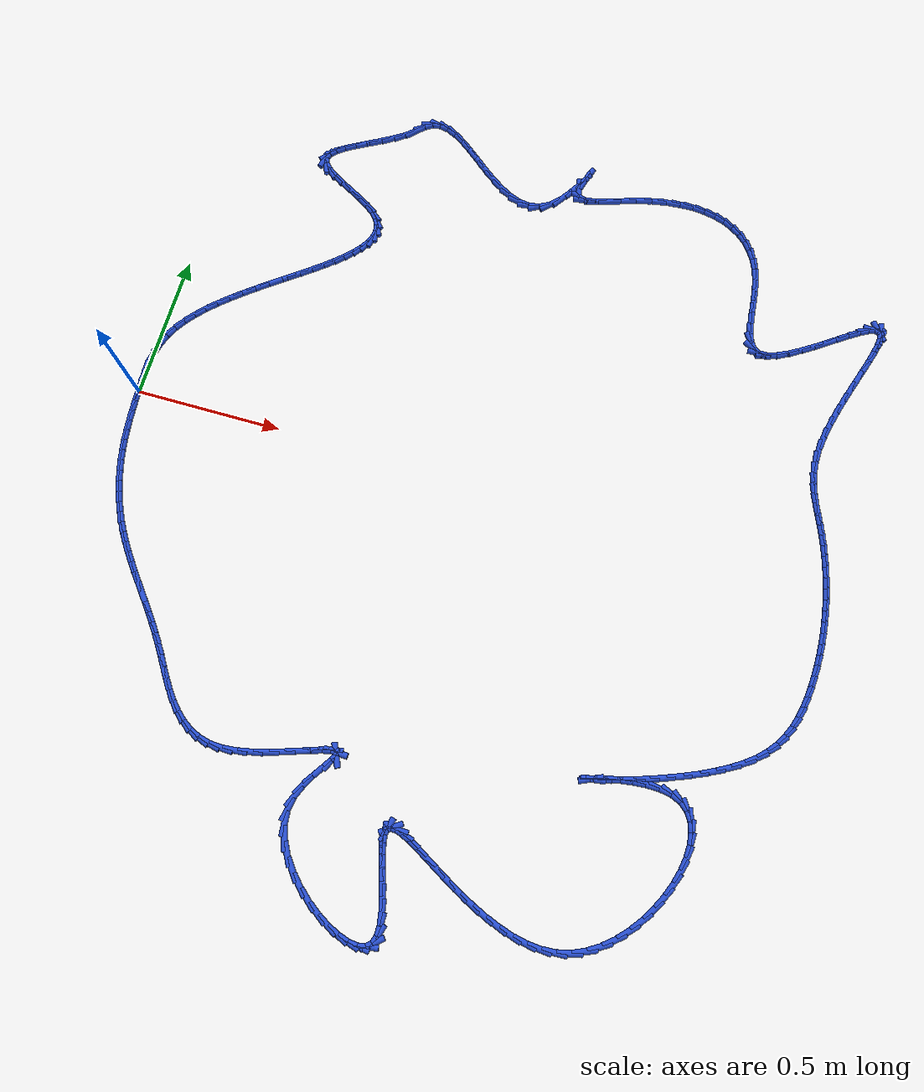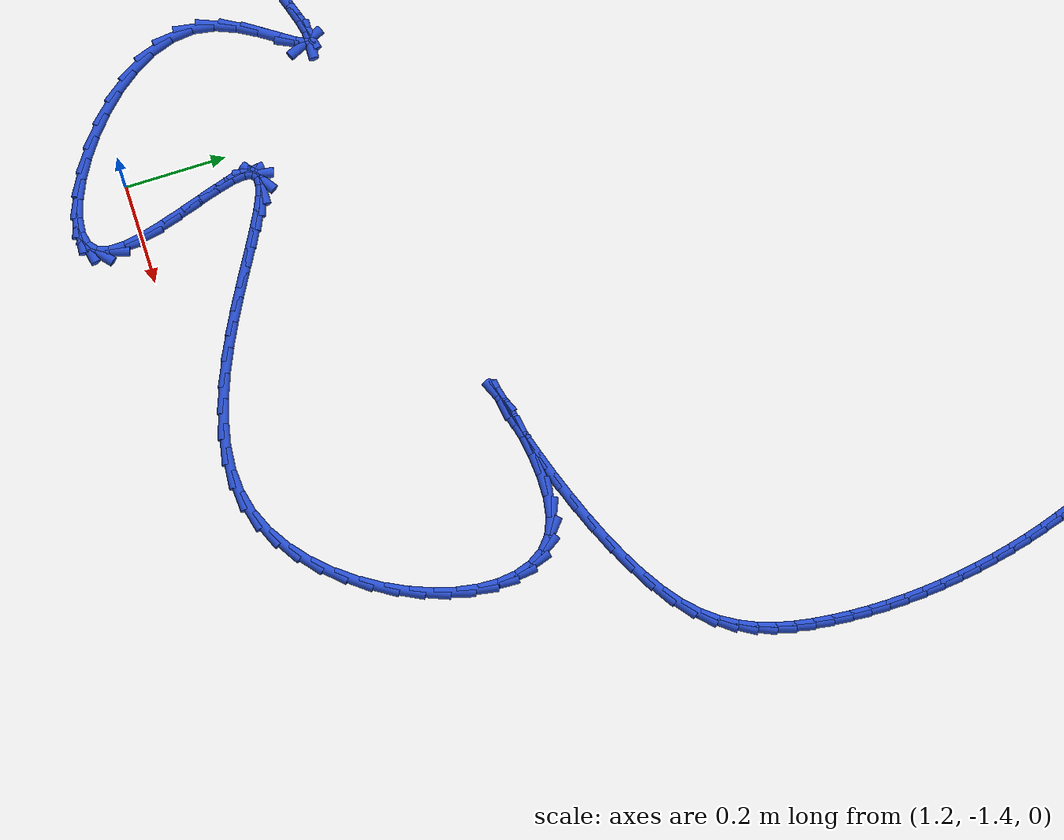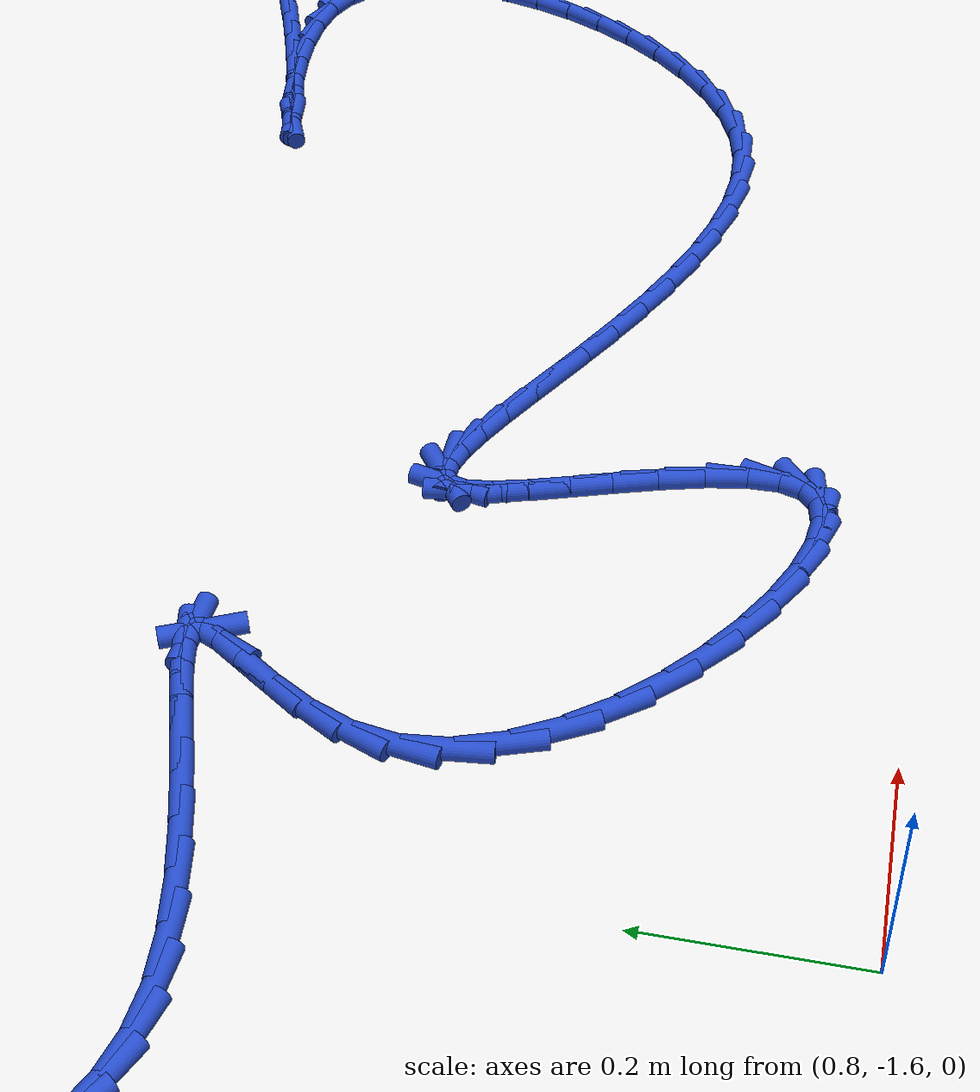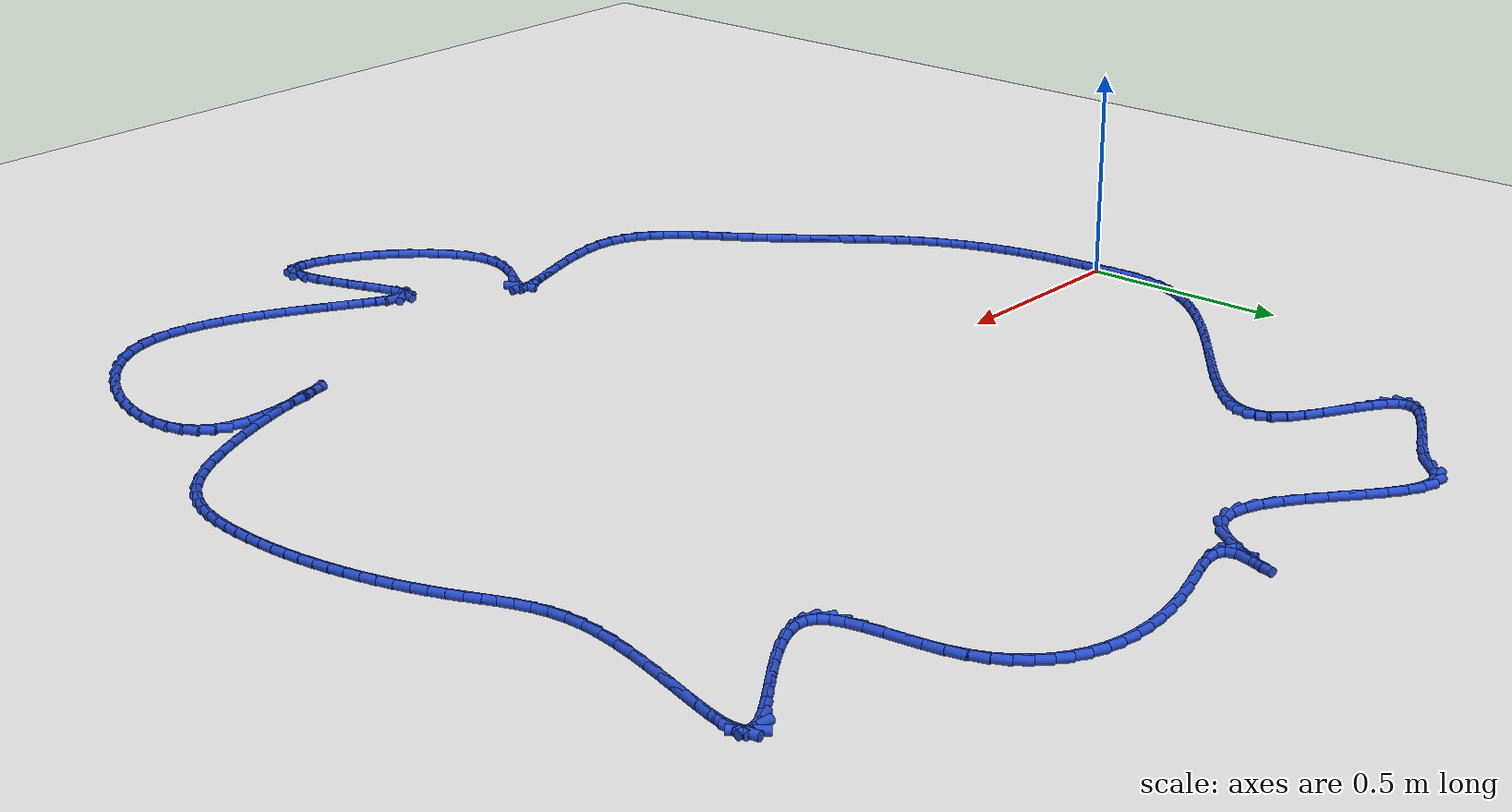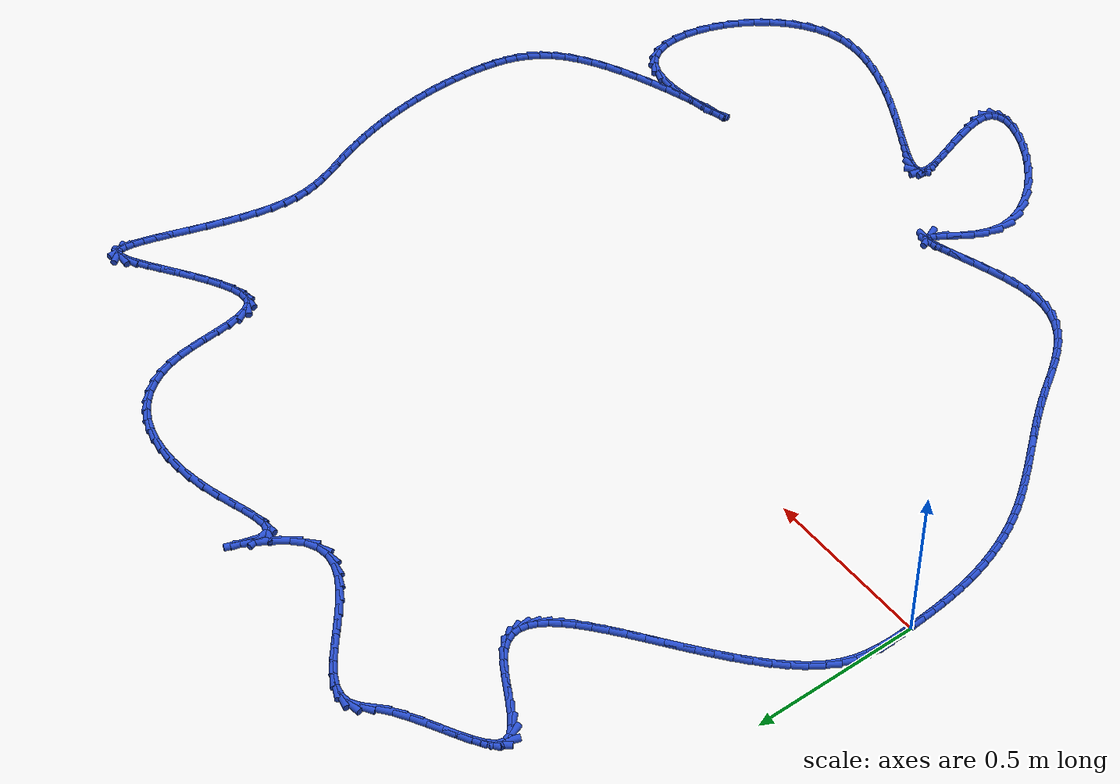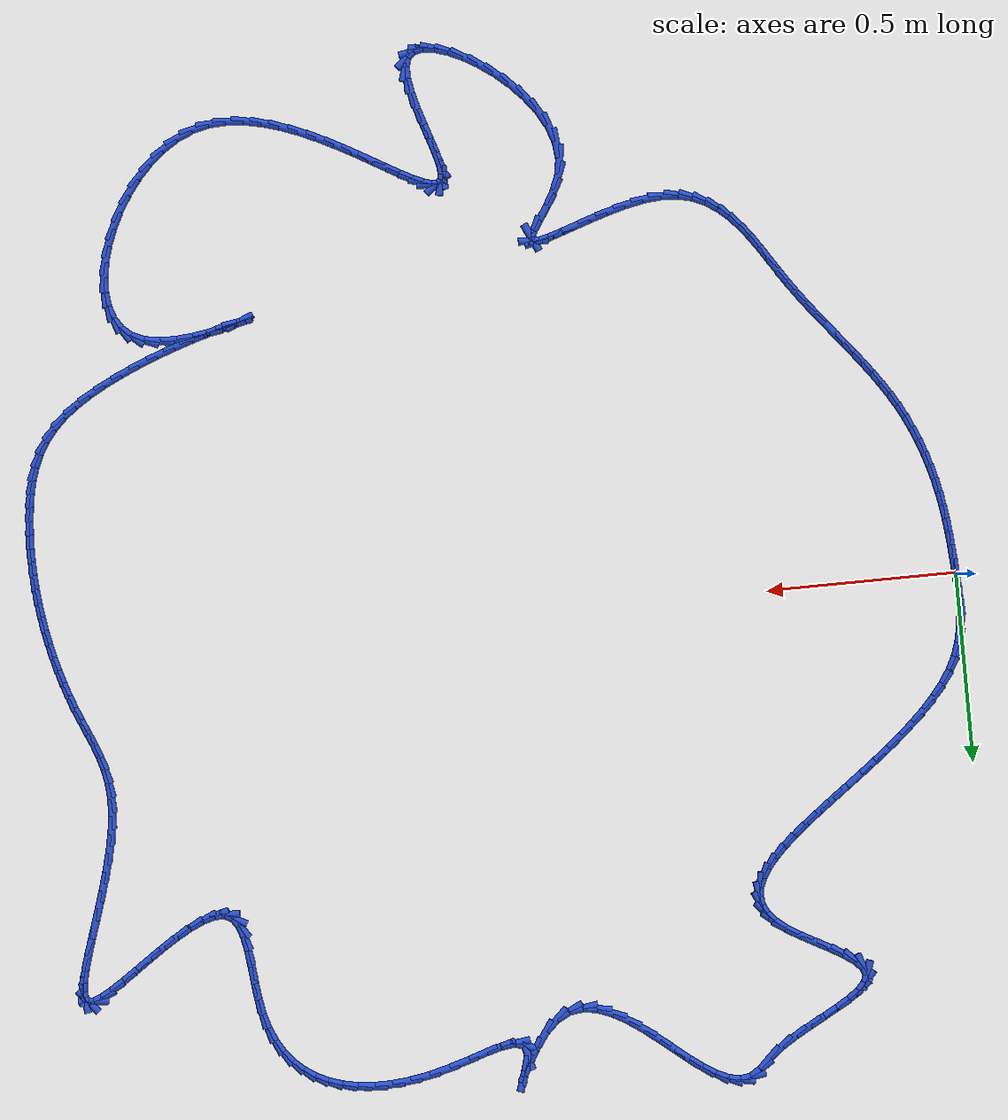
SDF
<sdf version="1.6">
 <world name="default">
  <light name="sun" type="directional">
   <pose>0 0 10 0 -0 0</pose>
   <diffuse>0.8 0.8 0.8 1</diffuse>
   <specular>0.2 0.2 0.2 1</specular>
   <attenuation>
    <range>1000</range>
    <constant>0.9</constant>
    <linear>0.01</linear>
    <quadratic>0.001</quadratic>
   </attenuation>
   <direction>-0.5 0.1 -0.9</direction>
  </light>
  <model name="ground_plane">
   <static>1</static>
   <link name="link">
    <collision name="collision">
     <geometry><plane><normal>0 0 1</normal><size>100 100</size></plane></geometry>
     <surface><friction><ode><mu>100</mu><mu2>50</mu2></ode></friction></surface>
    </collision>
    <visual name="visual">
     <cast_shadows>0</cast_shadows>
     <geometry><plane><normal>0 0 1</normal><size>100 100</size></plane></geometry>
     <material>
      <script><uri>file://media/materials/scripts/gazebo.material</uri><name>Gazebo/WhiteGlow</name></script>
     </material>
    </visual>
   </link>
  </model>
  <gravity>0 0 -9.8</gravity>
  <magnetic_field>6e-06 2.3e-05 -4.2e-05</magnetic_field>
  <atmosphere type="adiabatic"/>
  <physics name="default_physics" default="0" type="ode">
   <max_step_size>0.001</max_step_size>
   <real_time_factor>1</real_time_factor>
   <real_time_update_rate>1000</real_time_update_rate>
  </physics>
  <scene><ambient>0.4 0.4 0.4 1</ambient><background>0.7 0.7 0.7 1</background><shadows>1</shadows></scene>
  <spherical_coordinates>
   <surface_model>EARTH_WGS84</surface_model>
   <latitude_deg>0</latitude_deg>
   <longitude_deg>0</longitude_deg>
   <elevation>0</elevation>
   <heading_deg>0</heading_deg>
  </spherical_coordinates>
  <model name="line">
   <link name="link_0">
    <pose>4.0549161250957866e-17 -6.938893903907228e-18 0.01 0 1.57 -1.52185023954393</pose>
    <collision name="collision">
     <geometry><cylinder><radius>0.01</radius><length>0.08</length></cylinder></geometry>
    </collision>
    <visual name="visual">
     <material>
      <script><name>Gazebo/Blue</name><uri>file://media/materials/scripts/gazebo.material</uri></script>
     </material>
     <geometry><cylinder><radius>0.01</radius><length>0.08</length></cylinder></geometry>
    </visual>
   </link>
   <link name="link_1">
    <pose>-0.0017894815718800692 0.03653105717077302 0.01 0 1.57 -1.5514126485488813</pose>
    <collision name="collision">
     <geometry><cylinder><radius>0.01</radius><length>0.08</length></cylinder></geometry>
    </collision>
    <visual name="visual">
     <material>
      <script><name>Gazebo/Blue</name><uri>file://media/materials/scripts/gazebo.material</uri></script>
     </material>
     <geometry><cylinder><radius>0.01</radius><length>0.08</length></cylinder></geometry>
    </visual>
   </link>
   <link name="link_2">
    <pose>-0.0024977876290873365 0.07306784529206682 0.01 0 1.57 1.53710981820446</pose>
    <collision name="collision">
     <geometry><cylinder><radius>0.01</radius><length>0.08</length></cylinder></geometry>
    </collision>
    <visual name="visual">
     <material>
      <script><name>Gazebo/Blue</name><uri>file://media/materials/scripts/gazebo.material</uri></script>
     </material>
     <geometry><cylinder><radius>0.01</radius><length>0.08</length></cylinder></geometry>
    </visual>
   </link>
   <link name="link_3">
    <pose>-0.0012706008610770033 0.10948368617913154 0.01 0 1.57 1.4601853632934978</pose>
    <collision name="collision">
     <geometry><cylinder><radius>0.01</radius><length>0.08</length></cylinder></geometry>
    </collision>
    <visual name="visual">
     <material>
      <script><name>Gazebo/Blue</name><uri>file://media/materials/scripts/gazebo.material</uri></script>
     </material>
     <geometry><cylinder><radius>0.01</radius><length>0.08</length></cylinder></geometry>
    </visual>
   </link>
   <link name="link_4">
    <pose>0.0027463960426956906 0.14565190164721714 0.01 0 1.57 1.3599433964282441</pose>
    <collision name="collision">
     <geometry><cylinder><radius>0.01</radius><length>0.08</length></cylinder></geometry>
    </collision>
    <visual name="visual">
     <material>
      <script><name>Gazebo/Blue</name><uri>file://media/materials/scripts/gazebo.material</uri></script>
     </material>
     <geometry><cylinder><radius>0.01</radius><length>0.08</length></cylinder></geometry>
    </visual>
   </link>
   <link name="link_5">
    <pose>0.010407520392775503 0.18144581351157385 0.01 0 1.57 1.239000416244004</pose>
    <collision name="collision">
     <geometry><cylinder><radius>0.01</radius><length>0.08</length></cylinder></geometry>
    </collision>
    <visual name="visual">
     <material>
      <script><name>Gazebo/Blue</name><uri>file://media/materials/scripts/gazebo.material</uri></script>
     </material>
     <geometry><cylinder><radius>0.01</radius><length>0.08</length></cylinder></geometry>
    </visual>
   </link>
   <link name="link_6">
    <pose>0.022567089499707205 0.21673874358745163 0.01 0 1.57 1.1064730745596445</pose>
    <collision name="collision">
     <geometry><cylinder><radius>0.01</radius><length>0.08</length></cylinder></geometry>
    </collision>
    <visual name="visual">
     <material>
      <script><name>Gazebo/Blue</name><uri>file://media/materials/scripts/gazebo.material</uri></script>
     </material>
     <geometry><cylinder><radius>0.01</radius><length>0.08</length></cylinder></geometry>
    </visual>
   </link>
   <link name="link_7">
    <pose>0.039935536010883205 0.25141704141289367 0.01 0 1.57 0.9900699989752234</pose>
    <collision name="collision">
     <geometry><cylinder><radius>0.01</radius><length>0.08</length></cylinder></geometry>
    </collision>
    <visual name="visual">
     <material>
      <script><name>Gazebo/Blue</name><uri>file://media/materials/scripts/gazebo.material</uri></script>
     </material>
     <geometry><cylinder><radius>0.01</radius><length>0.08</length></cylinder></geometry>
    </visual>
   </link>
   <link name="link_8">
    <pose>0.06227039153271126 0.28545333487096836 0.01 0 1.57 0.8969722031873676</pose>
    <collision name="collision">
     <geometry><cylinder><radius>0.01</radius><length>0.08</length></cylinder></geometry>
    </collision>
    <visual name="visual">
     <material>
      <script><name>Gazebo/Blue</name><uri>file://media/materials/scripts/gazebo.material</uri></script>
     </material>
     <geometry><cylinder><radius>0.01</radius><length>0.08</length></cylinder></geometry>
    </visual>
   </link>
   <link name="link_9">
    <pose>0.08894179943286262 0.31885532706733505 0.01 0 1.57 0.8233596326819432</pose>
    <collision name="collision">
     <geometry><cylinder><radius>0.01</radius><length>0.08</length></cylinder></geometry>
    </collision>
    <visual name="visual">
     <material>
      <script><name>Gazebo/Blue</name><uri>file://media/materials/scripts/gazebo.material</uri></script>
     </material>
     <geometry><cylinder><radius>0.01</radius><length>0.08</length></cylinder></geometry>
    </visual>
   </link>
   <link name="link_10">
    <pose>0.11931878188064625 0.35163082262411266 0.01 0 1.57 0.7656658133431868</pose>
    <collision name="collision">
     <geometry><cylinder><radius>0.01</radius><length>0.08</length></cylinder></geometry>
    </collision>
    <visual name="visual">
     <material>
      <script><name>Gazebo/Blue</name><uri>file://media/materials/scripts/gazebo.material</uri></script>
     </material>
     <geometry><cylinder><radius>0.01</radius><length>0.08</length></cylinder></geometry>
    </visual>
   </link>
   <link name="link_11">
    <pose>0.1527703610453711 0.3837876261634192 0.01 0 1.57 0.7209972789925128</pose>
    <collision name="collision">
     <geometry><cylinder><radius>0.01</radius><length>0.08</length></cylinder></geometry>
    </collision>
    <visual name="visual">
     <material>
      <script><name>Gazebo/Blue</name><uri>file://media/materials/scripts/gazebo.material</uri></script>
     </material>
     <geometry><cylinder><radius>0.01</radius><length>0.08</length></cylinder></geometry>
    </visual>
   </link>
   <link name="link_12">
    <pose>0.18866555909634602 0.4153335423073732 0.01 0 1.57 0.6871728330269824</pose>
    <collision name="collision">
     <geometry><cylinder><radius>0.01</radius><length>0.08</length></cylinder></geometry>
    </collision>
    <visual name="visual">
     <material>
      <script><name>Gazebo/Blue</name><uri>file://media/materials/scripts/gazebo.material</uri></script>
     </material>
     <geometry><cylinder><radius>0.01</radius><length>0.08</length></cylinder></geometry>
    </visual>
   </link>
   <link name="link_13">
    <pose>0.22637339820288008 0.4462763756780934 0.01 0 1.57 0.6626459752604367</pose>
    <collision name="collision">
     <geometry><cylinder><radius>0.01</radius><length>0.08</length></cylinder></geometry>
    </collision>
    <visual name="visual">
     <material>
      <script><name>Gazebo/Blue</name><uri>file://media/materials/scripts/gazebo.material</uri></script>
     </material>
     <geometry><cylinder><radius>0.01</radius><length>0.08</length></cylinder></geometry>
    </visual>
   </link>
   <link name="link_14">
    <pose>0.2652629005342819 0.47662393089769783 0.01 0 1.57 0.6464146395870033</pose>
    <collision name="collision">
     <geometry><cylinder><radius>0.01</radius><length>0.08</length></cylinder></geometry>
    </collision>
    <visual name="visual">
     <material>
      <script><name>Gazebo/Blue</name><uri>file://media/materials/scripts/gazebo.material</uri></script>
     </material>
     <geometry><cylinder><radius>0.01</radius><length>0.08</length></cylinder></geometry>
    </visual>
   </link>
   <link name="link_15">
    <pose>0.30470308825986075 0.5063840125883051 0.01 0 1.57 0.6379577326848062</pose>
    <collision name="collision">
     <geometry><cylinder><radius>0.01</radius><length>0.08</length></cylinder></geometry>
    </collision>
    <visual name="visual">
     <material>
      <script><name>Gazebo/Blue</name><uri>file://media/materials/scripts/gazebo.material</uri></script>
     </material>
     <geometry><cylinder><radius>0.01</radius><length>0.08</length></cylinder></geometry>
    </visual>
   </link>
   <link name="link_16">
    <pose>0.34406298354892534 0.5355644253720336 0.01 0 1.57 0.6372135277538157</pose>
    <collision name="collision">
     <geometry><cylinder><radius>0.01</radius><length>0.08</length></cylinder></geometry>
    </collision>
    <visual name="visual">
     <material>
      <script><name>Gazebo/Blue</name><uri>file://media/materials/scripts/gazebo.material</uri></script>
     </material>
     <geometry><cylinder><radius>0.01</radius><length>0.08</length></cylinder></geometry>
    </visual>
   </link>
   <link name="link_17">
    <pose>0.38271160857078473 0.5641729738710021 0.01 0 1.57 0.6446102346289906</pose>
    <collision name="collision">
     <geometry><cylinder><radius>0.01</radius><length>0.08</length></cylinder></geometry>
    </collision>
    <visual name="visual">
     <material>
      <script><name>Gazebo/Blue</name><uri>file://media/materials/scripts/gazebo.material</uri></script>
     </material>
     <geometry><cylinder><radius>0.01</radius><length>0.08</length></cylinder></geometry>
    </visual>
   </link>
   <link name="link_18">
    <pose>0.4200179854947478 0.5922174627073284 0.01 0 1.57 0.6611647308605674</pose>
    <collision name="collision">
     <geometry><cylinder><radius>0.01</radius><length>0.08</length></cylinder></geometry>
    </collision>
    <visual name="visual">
     <material>
      <script><name>Gazebo/Blue</name><uri>file://media/materials/scripts/gazebo.material</uri></script>
     </material>
     <geometry><cylinder><radius>0.01</radius><length>0.08</length></cylinder></geometry>
    </visual>
   </link>
   <link name="link_19">
    <pose>0.4553511364901233 0.6197056965031313 0.01 0 1.57 0.6886791478817208</pose>
    <collision name="collision">
     <geometry><cylinder><radius>0.01</radius><length>0.08</length></cylinder></geometry>
    </collision>
    <visual name="visual">
     <material>
      <script><name>Gazebo/Blue</name><uri>file://media/materials/scripts/gazebo.material</uri></script>
     </material>
     <geometry><cylinder><radius>0.01</radius><length>0.08</length></cylinder></geometry>
    </visual>
   </link>
   <link name="link_20">
    <pose>0.48808008372622036 0.6466454798805293 0.01 0 1.57 0.7300875339702076</pose>
    <collision name="collision">
     <geometry><cylinder><radius>0.01</radius><length>0.08</length></cylinder></geometry>
    </collision>
    <visual name="visual">
     <material>
      <script><name>Gazebo/Blue</name><uri>file://media/materials/scripts/gazebo.material</uri></script>
     </material>
     <geometry><cylinder><radius>0.01</radius><length>0.08</length></cylinder></geometry>
    </visual>
   </link>
   <link name="link_21">
    <pose>0.517573849372348 0.6730446174616407 0.01 0 1.57 0.7900334398047495</pose>
    <collision name="collision">
     <geometry><cylinder><radius>0.01</radius><length>0.08</length></cylinder></geometry>
    </collision>
    <visual name="visual">
     <material>
      <script><name>Gazebo/Blue</name><uri>file://media/materials/scripts/gazebo.material</uri></script>
     </material>
     <geometry><cylinder><radius>0.01</radius><length>0.08</length></cylinder></geometry>
    </visual>
   </link>
   <link name="link_22">
    <pose>0.5432014555978149 0.6989109138685841 0.01 0 1.57 0.8757611371465852</pose>
    <collision name="collision">
     <geometry><cylinder><radius>0.01</radius><length>0.08</length></cylinder></geometry>
    </collision>
    <visual name="visual">
     <material>
      <script><name>Gazebo/Blue</name><uri>file://media/materials/scripts/gazebo.material</uri></script>
     </material>
     <geometry><cylinder><radius>0.01</radius><length>0.08</length></cylinder></geometry>
    </visual>
   </link>
   <link name="link_23">
    <pose>0.5643319245719303 0.7242521737234777 0.01 0 1.57 0.998204257731185</pose>
    <collision name="collision">
     <geometry><cylinder><radius>0.01</radius><length>0.08</length></cylinder></geometry>
    </collision>
    <visual name="visual">
     <material>
      <script><name>Gazebo/Blue</name><uri>file://media/materials/scripts/gazebo.material</uri></script>
     </material>
     <geometry><cylinder><radius>0.01</radius><length>0.08</length></cylinder></geometry>
    </visual>
   </link>
   <link name="link_24">
    <pose>0.5803342784640025 0.74907620164844 0.01 0 1.57 1.1720805567565529</pose>
    <collision name="collision">
     <geometry><cylinder><radius>0.01</radius><length>0.08</length></cylinder></geometry>
    </collision>
    <visual name="visual">
     <material>
      <script><name>Gazebo/Blue</name><uri>file://media/materials/scripts/gazebo.material</uri></script>
     </material>
     <geometry><cylinder><radius>0.01</radius><length>0.08</length></cylinder></geometry>
    </visual>
   </link>
   <link name="link_25">
    <pose>0.5905775394433411 0.7733908022655895 0.01 0 1.57 1.4103762416425547</pose>
    <collision name="collision">
     <geometry><cylinder><radius>0.01</radius><length>0.08</length></cylinder></geometry>
    </collision>
    <visual name="visual">
     <material>
      <script><name>Gazebo/Blue</name><uri>file://media/materials/scripts/gazebo.material</uri></script>
     </material>
     <geometry><cylinder><radius>0.01</radius><length>0.08</length></cylinder></geometry>
    </visual>
   </link>
   <link name="link_26">
    <pose>0.5944307296792548 0.7972037801970446 0.01 0 1.57 -1.4357749925882015</pose>
    <collision name="collision">
     <geometry><cylinder><radius>0.01</radius><length>0.08</length></cylinder></geometry>
    </collision>
    <visual name="visual">
     <material>
      <script><name>Gazebo/Blue</name><uri>file://media/materials/scripts/gazebo.material</uri></script>
     </material>
     <geometry><cylinder><radius>0.01</radius><length>0.08</length></cylinder></geometry>
    </visual>
   </link>
   <link name="link_27">
    <pose>0.5912628713410522 0.8205229400649234 0.01 0 1.57 -1.128272459672479</pose>
    <collision name="collision">
     <geometry><cylinder><radius>0.01</radius><length>0.08</length></cylinder></geometry>
    </collision>
    <visual name="visual">
     <material>
      <script><name>Gazebo/Blue</name><uri>file://media/materials/scripts/gazebo.material</uri></script>
     </material>
     <geometry><cylinder><radius>0.01</radius><length>0.08</length></cylinder></geometry>
    </visual>
   </link>
   <link name="link_28">
    <pose>0.5804429865980428 0.8433560864913452 0.01 0 1.57 -0.8636801971120777</pose>
    <collision name="collision">
     <geometry><cylinder><radius>0.01</radius><length>0.08</length></cylinder></geometry>
    </collision>
    <visual name="visual">
     <material>
      <script><name>Gazebo/Blue</name><uri>file://media/materials/scripts/gazebo.material</uri></script>
     </material>
     <geometry><cylinder><radius>0.01</radius><length>0.08</length></cylinder></geometry>
    </visual>
   </link>
   <link name="link_29">
    <pose>0.5613400976195351 0.8657110240984276 0.01 0 1.57 -0.6682199195717694</pose>
    <collision name="collision">
     <geometry><cylinder><radius>0.01</radius><length>0.08</length></cylinder></geometry>
    </collision>
    <visual name="visual">
     <material>
      <script><name>Gazebo/Blue</name><uri>file://media/materials/scripts/gazebo.material</uri></script>
     </material>
     <geometry><cylinder><radius>0.01</radius><length>0.08</length></cylinder></geometry>
    </visual>
   </link>
   <link name="link_30">
    <pose>0.5336132605426608 0.8875975044585684 0.01 0 1.57 -0.5584790025619196</pose>
    <collision name="collision">
     <geometry><cylinder><radius>0.01</radius><length>0.08</length></cylinder></geometry>
    </collision>
    <visual name="visual">
     <material>
      <script><name>Gazebo/Blue</name><uri>file://media/materials/scripts/gazebo.material</uri></script>
     </material>
     <geometry><cylinder><radius>0.01</radius><length>0.08</length></cylinder></geometry>
    </visual>
   </link>
   <link name="link_31">
    <pose>0.4992941514390502 0.909041206151193 0.01 0 1.57 -0.5086994821933081</pose>
    <collision name="collision">
     <geometry><cylinder><radius>0.01</radius><length>0.08</length></cylinder></geometry>
    </collision>
    <visual name="visual">
     <material>
      <script><name>Gazebo/Blue</name><uri>file://media/materials/scripts/gazebo.material</uri></script>
     </material>
     <geometry><cylinder><radius>0.01</radius><length>0.08</length></cylinder></geometry>
    </visual>
   </link>
   <link name="link_32">
    <pose>0.4615746243389148 0.9300755958393682 0.01 0 1.57 -0.49883553529728303</pose>
    <collision name="collision">
     <geometry><cylinder><radius>0.01</radius><length>0.08</length></cylinder></geometry>
    </collision>
    <visual name="visual">
     <material>
      <script><name>Gazebo/Blue</name><uri>file://media/materials/scripts/gazebo.material</uri></script>
     </material>
     <geometry><cylinder><radius>0.01</radius><length>0.08</length></cylinder></geometry>
    </visual>
   </link>
   <link name="link_33">
    <pose>0.4236544309182554 0.9507341932017568 0.01 0 1.57 -0.5269130423250743</pose>
    <collision name="collision">
     <geometry><cylinder><radius>0.01</radius><length>0.08</length></cylinder></geometry>
    </collision>
    <visual name="visual">
     <material>
      <script><name>Gazebo/Blue</name><uri>file://media/materials/scripts/gazebo.material</uri></script>
     </material>
     <geometry><cylinder><radius>0.01</radius><length>0.08</length></cylinder></geometry>
    </visual>
   </link>
   <link name="link_34">
    <pose>0.38873332285307316 0.9710505179170217 0.01 0 1.57 -0.6084319466866757</pose>
    <collision name="collision">
     <geometry><cylinder><radius>0.01</radius><length>0.08</length></cylinder></geometry>
    </collision>
    <visual name="visual">
     <material>
      <script><name>Gazebo/Blue</name><uri>file://media/materials/scripts/gazebo.material</uri></script>
     </material>
     <geometry><cylinder><radius>0.01</radius><length>0.08</length></cylinder></geometry>
    </visual>
   </link>
   <link name="link_35">
    <pose>0.36001105181936877 0.9910580896638257 0.01 0 1.57 -0.7958611140555002</pose>
    <collision name="collision">
     <geometry><cylinder><radius>0.01</radius><length>0.08</length></cylinder></geometry>
    </collision>
    <visual name="visual">
     <material>
      <script><name>Gazebo/Blue</name><uri>file://media/materials/scripts/gazebo.material</uri></script>
     </material>
     <geometry><cylinder><radius>0.01</radius><length>0.08</length></cylinder></geometry>
    </visual>
   </link>
   <link name="link_36">
    <pose>0.34068736949314327 1.0107904281208315 0.01 0 1.57 -1.2360688434260683</pose>
    <collision name="collision">
     <geometry><cylinder><radius>0.01</radius><length>0.08</length></cylinder></geometry>
    </collision>
    <visual name="visual">
     <material>
      <script><name>Gazebo/Blue</name><uri>file://media/materials/scripts/gazebo.material</uri></script>
     </material>
     <geometry><cylinder><radius>0.01</radius><length>0.08</length></cylinder></geometry>
    </visual>
   </link>
   <link name="link_37">
    <pose>0.3339076174800267 1.030282802776633 0.01 0 1.57 1.2392886105134389</pose>
    <collision name="collision">
     <geometry><cylinder><radius>0.01</radius><length>0.08</length></cylinder></geometry>
    </collision>
    <visual name="visual">
     <material>
      <script><name>Gazebo/Blue</name><uri>file://media/materials/scripts/gazebo.material</uri></script>
     </material>
     <geometry><cylinder><radius>0.01</radius><length>0.08</length></cylinder></geometry>
    </visual>
   </link>
   <link name="link_38">
    <pose>0.34057149516570917 1.0496427022334927 0.01 0 1.57 0.8232768029697289</pose>
    <collision name="collision">
     <geometry><cylinder><radius>0.01</radius><length>0.08</length></cylinder></geometry>
    </collision>
    <visual name="visual">
     <material>
      <script><name>Gazebo/Blue</name><uri>file://media/materials/scripts/gazebo.material</uri></script>
     </material>
     <geometry><cylinder><radius>0.01</radius><length>0.08</length></cylinder></geometry>
    </visual>
   </link>
   <link name="link_39">
    <pose>0.35858373851987274 1.0690739321300435 0.01 0 1.57 0.6296447900452782</pose>
    <collision name="collision">
     <geometry><cylinder><radius>0.01</radius><length>0.08</length></cylinder></geometry>
    </collision>
    <visual name="visual">
     <material>
      <script><name>Gazebo/Blue</name><uri>file://media/materials/scripts/gazebo.material</uri></script>
     </material>
     <geometry><cylinder><radius>0.01</radius><length>0.08</length></cylinder></geometry>
    </visual>
   </link>
   <link name="link_40">
    <pose>0.385640903360843 1.088786993109975 0.01 0 1.57 0.5388125860778482</pose>
    <collision name="collision">
     <geometry><cylinder><radius>0.01</radius><length>0.08</length></cylinder></geometry>
    </collision>
    <visual name="visual">
     <material>
      <script><name>Gazebo/Blue</name><uri>file://media/materials/scripts/gazebo.material</uri></script>
     </material>
     <geometry><cylinder><radius>0.01</radius><length>0.08</length></cylinder></geometry>
    </visual>
   </link>
   <link name="link_41">
    <pose>0.41943954550694595 1.1089923858169755 0.01 0 1.57 0.5003913533586438</pose>
    <collision name="collision">
     <geometry><cylinder><radius>0.01</radius><length>0.08</length></cylinder></geometry>
    </collision>
    <visual name="visual">
     <material>
      <script><name>Gazebo/Blue</name><uri>file://media/materials/scripts/gazebo.material</uri></script>
     </material>
     <geometry><cylinder><radius>0.01</radius><length>0.08</length></cylinder></geometry>
    </visual>
   </link>
   <link name="link_42">
    <pose>0.457676220776507 1.1299006108947345 0.01 0 1.57 0.495537356174492</pose>
    <collision name="collision">
     <geometry><cylinder><radius>0.01</radius><length>0.08</length></cylinder></geometry>
    </collision>
    <visual name="visual">
     <material>
      <script><name>Gazebo/Blue</name><uri>file://media/materials/scripts/gazebo.material</uri></script>
     </material>
     <geometry><cylinder><radius>0.01</radius><length>0.08</length></cylinder></geometry>
    </visual>
   </link>
   <link name="link_43">
    <pose>0.4980474849878519 1.15172216898694 0.01 0 1.57 0.5186319276873228</pose>
    <collision name="collision">
     <geometry><cylinder><radius>0.01</radius><length>0.08</length></cylinder></geometry>
    </collision>
    <visual name="visual">
     <material>
      <script><name>Gazebo/Blue</name><uri>file://media/materials/scripts/gazebo.material</uri></script>
     </material>
     <geometry><cylinder><radius>0.01</radius><length>0.08</length></cylinder></geometry>
    </visual>
   </link>
   <link name="link_44">
    <pose>0.538249893959307 1.1746675607372814 0.01 0 1.57 0.5717997279888994</pose>
    <collision name="collision">
     <geometry><cylinder><radius>0.01</radius><length>0.08</length></cylinder></geometry>
    </collision>
    <visual name="visual">
     <material>
      <script><name>Gazebo/Blue</name><uri>file://media/materials/scripts/gazebo.material</uri></script>
     </material>
     <geometry><cylinder><radius>0.01</radius><length>0.08</length></cylinder></geometry>
    </visual>
   </link>
   <link name="link_45">
    <pose>0.5759800035091973 1.1989472867894477 0.01 0 1.57 0.6646892120676976</pose>
    <collision name="collision">
     <geometry><cylinder><radius>0.01</radius><length>0.08</length></cylinder></geometry>
    </collision>
    <visual name="visual">
     <material>
      <script><name>Gazebo/Blue</name><uri>file://media/materials/scripts/gazebo.material</uri></script>
     </material>
     <geometry><cylinder><radius>0.01</radius><length>0.08</length></cylinder></geometry>
    </visual>
   </link>
   <link name="link_46">
    <pose>0.608934369455849 1.2247718477871272 0.01 0 1.57 0.7715759841904085</pose>
    <collision name="collision">
     <geometry><cylinder><radius>0.01</radius><length>0.08</length></cylinder></geometry>
    </collision>
    <visual name="visual">
     <material>
      <script><name>Gazebo/Blue</name><uri>file://media/materials/scripts/gazebo.material</uri></script>
     </material>
     <geometry><cylinder><radius>0.01</radius><length>0.08</length></cylinder></geometry>
    </visual>
   </link>
   <link name="link_47">
    <pose>0.6358750537948947 1.2509778818736104 0.01 0 1.57 0.5727125876559368</pose>
    <collision name="collision">
     <geometry><cylinder><radius>0.01</radius><length>0.08</length></cylinder></geometry>
    </collision>
    <visual name="visual">
     <material>
      <script><name>Gazebo/Blue</name><uri>file://media/materials/scripts/gazebo.material</uri></script>
     </material>
     <geometry><cylinder><radius>0.01</radius><length>0.08</length></cylinder></geometry>
    </visual>
   </link>
   <link name="link_48">
    <pose>0.6622998785806712 1.268016668502915 0.01 0 1.57 0.15399709920893923</pose>
    <collision name="collision">
     <geometry><cylinder><radius>0.01</radius><length>0.08</length></cylinder></geometry>
    </collision>
    <visual name="visual">
     <material>
      <script><name>Gazebo/Blue</name><uri>file://media/materials/scripts/gazebo.material</uri></script>
     </material>
     <geometry><cylinder><radius>0.01</radius><length>0.08</length></cylinder></geometry>
    </visual>
   </link>
   <link name="link_49">
    <pose>0.6910181468104952 1.2724744936100958 0.01 0 1.57 -0.1992596876874177</pose>
    <collision name="collision">
     <geometry><cylinder><radius>0.01</radius><length>0.08</length></cylinder></geometry>
    </collision>
    <visual name="visual">
     <material>
      <script><name>Gazebo/Blue</name><uri>file://media/materials/scripts/gazebo.material</uri></script>
     </material>
     <geometry><cylinder><radius>0.01</radius><length>0.08</length></cylinder></geometry>
    </visual>
   </link>
   <link name="link_50">
    <pose>0.7217977998325201 1.2662588683845148 0.01 0 1.57 -0.42978826728244734</pose>
    <collision name="collision">
     <geometry><cylinder><radius>0.01</radius><length>0.08</length></cylinder></geometry>
    </collision>
    <visual name="visual">
     <material>
      <script><name>Gazebo/Blue</name><uri>file://media/materials/scripts/gazebo.material</uri></script>
     </material>
     <geometry><cylinder><radius>0.01</radius><length>0.08</length></cylinder></geometry>
    </visual>
   </link>
   <link name="link_51">
    <pose>0.7543798264323355 1.25132441489047 0.01 0 1.57 -0.5663641937381623</pose>
    <collision name="collision">
     <geometry><cylinder><radius>0.01</radius><length>0.08</length></cylinder></geometry>
    </collision>
    <visual name="visual">
     <material>
      <script><name>Gazebo/Blue</name><uri>file://media/materials/scripts/gazebo.material</uri></script>
     </material>
     <geometry><cylinder><radius>0.01</radius><length>0.08</length></cylinder></geometry>
    </visual>
   </link>
   <link name="link_52">
    <pose>0.7885052153955313 1.22962575519226 0.01 0 1.57 -0.6426137799060258</pose>
    <collision name="collision">
     <geometry><cylinder><radius>0.01</radius><length>0.08</length></cylinder></geometry>
    </collision>
    <visual name="visual">
     <material>
      <script><name>Gazebo/Blue</name><uri>file://media/materials/scripts/gazebo.material</uri></script>
     </material>
     <geometry><cylinder><radius>0.01</radius><length>0.08</length></cylinder></geometry>
    </visual>
   </link>
   <link name="link_53">
    <pose>0.8239149555076982 1.2031175113541839 0.01 0 1.57 -0.6783310738397543</pose>
    <collision name="collision">
     <geometry><cylinder><radius>0.01</radius><length>0.08</length></cylinder></geometry>
    </collision>
    <visual name="visual">
     <material>
      <script><name>Gazebo/Blue</name><uri>file://media/materials/scripts/gazebo.material</uri></script>
     </material>
     <geometry><cylinder><radius>0.01</radius><length>0.08</length></cylinder></geometry>
    </visual>
   </link>
   <link name="link_54">
    <pose>0.8603500355544256 1.1737543054405393 0.01 0 1.57 -0.6829218465158536</pose>
    <collision name="collision">
     <geometry><cylinder><radius>0.01</radius><length>0.08</length></cylinder></geometry>
    </collision>
    <visual name="visual">
     <material>
      <script><name>Gazebo/Blue</name><uri>file://media/materials/scripts/gazebo.material</uri></script>
     </material>
     <geometry><cylinder><radius>0.01</radius><length>0.08</length></cylinder></geometry>
    </visual>
   </link>
   <link name="link_55">
    <pose>0.8975514443213037 1.143490759515624 0.01 0 1.57 -0.6590615180974684</pose>
    <collision name="collision">
     <geometry><cylinder><radius>0.01</radius><length>0.08</length></cylinder></geometry>
    </collision>
    <visual name="visual">
     <material>
      <script><name>Gazebo/Blue</name><uri>file://media/materials/scripts/gazebo.material</uri></script>
     </material>
     <geometry><cylinder><radius>0.01</radius><length>0.08</length></cylinder></geometry>
    </visual>
   </link>
   <link name="link_56">
    <pose>0.9352601705939225 1.1142814956437381 0.01 0 1.57 -0.6041615672631026</pose>
    <collision name="collision">
     <geometry><cylinder><radius>0.01</radius><length>0.08</length></cylinder></geometry>
    </collision>
    <visual name="visual">
     <material>
      <script><name>Gazebo/Blue</name><uri>file://media/materials/scripts/gazebo.material</uri></script>
     </material>
     <geometry><cylinder><radius>0.01</radius><length>0.08</length></cylinder></geometry>
    </visual>
   </link>
   <link name="link_57">
    <pose>0.9732172031578722 1.0880811358891784 0.01 0 1.57 -0.510225276558021</pose>
    <collision name="collision">
     <geometry><cylinder><radius>0.01</radius><length>0.08</length></cylinder></geometry>
    </collision>
    <visual name="visual">
     <material>
      <script><name>Gazebo/Blue</name><uri>file://media/materials/scripts/gazebo.material</uri></script>
     </material>
     <geometry><cylinder><radius>0.01</radius><length>0.08</length></cylinder></geometry>
    </visual>
   </link>
   <link name="link_58">
    <pose>1.0111635307987423 1.0668443023162446 0.01 0 1.57 -0.363183490446987</pose>
    <collision name="collision">
     <geometry><cylinder><radius>0.01</radius><length>0.08</length></cylinder></geometry>
    </collision>
    <visual name="visual">
     <material>
      <script><name>Gazebo/Blue</name><uri>file://media/materials/scripts/gazebo.material</uri></script>
     </material>
     <geometry><cylinder><radius>0.01</radius><length>0.08</length></cylinder></geometry>
    </visual>
   </link>
   <link name="link_59">
    <pose>1.0488401423021236 1.052525616989234 0.01 0 1.57 -0.14556404478726406</pose>
    <collision name="collision">
     <geometry><cylinder><radius>0.01</radius><length>0.08</length></cylinder></geometry>
    </collision>
    <visual name="visual">
     <material>
      <script><name>Gazebo/Blue</name><uri>file://media/materials/scripts/gazebo.material</uri></script>
     </material>
     <geometry><cylinder><radius>0.01</radius><length>0.08</length></cylinder></geometry>
    </visual>
   </link>
   <link name="link_60">
    <pose>1.085988026453605 1.0470797019724454 0.01 0 1.57 0.14693811745827254</pose>
    <collision name="collision">
     <geometry><cylinder><radius>0.01</radius><length>0.08</length></cylinder></geometry>
    </collision>
    <visual name="visual">
     <material>
      <script><name>Gazebo/Blue</name><uri>file://media/materials/scripts/gazebo.material</uri></script>
     </material>
     <geometry><cylinder><radius>0.01</radius><length>0.08</length></cylinder></geometry>
    </visual>
   </link>
   <link name="link_61">
    <pose>1.122348172038778 1.0524611793301777 0.01 0 1.57 0.4750626391697864</pose>
    <collision name="collision">
     <geometry><cylinder><radius>0.01</radius><length>0.08</length></cylinder></geometry>
    </collision>
    <visual name="visual">
     <material>
      <script><name>Gazebo/Blue</name><uri>file://media/materials/scripts/gazebo.material</uri></script>
     </material>
     <geometry><cylinder><radius>0.01</radius><length>0.08</length></cylinder></geometry>
    </visual>
   </link>
   <link name="link_62">
    <pose>1.1576615678432316 1.0706246711267289 0.01 0 1.57 0.7688002010265766</pose>
    <collision name="collision">
     <geometry><cylinder><radius>0.01</radius><length>0.08</length></cylinder></geometry>
    </collision>
    <visual name="visual">
     <material>
      <script><name>Gazebo/Blue</name><uri>file://media/materials/scripts/gazebo.material</uri></script>
     </material>
     <geometry><cylinder><radius>0.01</radius><length>0.08</length></cylinder></geometry>
    </visual>
   </link>
   <link name="link_63">
    <pose>1.1916681852753925 1.103520738332192 0.01 0 1.57 0.9641058865481967</pose>
    <collision name="collision">
     <geometry><cylinder><radius>0.01</radius><length>0.08</length></cylinder></geometry>
    </collision>
    <visual name="visual">
     <material>
      <script><name>Gazebo/Blue</name><uri>file://media/materials/scripts/gazebo.material</uri></script>
     </material>
     <geometry><cylinder><radius>0.01</radius><length>0.08</length></cylinder></geometry>
    </visual>
   </link>
   <link name="link_64">
    <pose>1.2229961047785605 1.1486615742011617 0.01 0 1.57 1.050769904820477</pose>
    <collision name="collision">
     <geometry><cylinder><radius>0.01</radius><length>0.08</length></cylinder></geometry>
    </collision>
    <visual name="visual">
     <material>
      <script><name>Gazebo/Blue</name><uri>file://media/materials/scripts/gazebo.material</uri></script>
     </material>
     <geometry><cylinder><radius>0.01</radius><length>0.08</length></cylinder></geometry>
    </visual>
   </link>
   <link name="link_65">
    <pose>1.2470400216768356 1.1906525739523408 0.01 0 1.57 1.069491855337708</pose>
    <collision name="collision">
     <geometry><cylinder><radius>0.01</radius><length>0.08</length></cylinder></geometry>
    </collision>
    <visual name="visual">
     <material>
      <script><name>Gazebo/Blue</name><uri>file://media/materials/scripts/gazebo.material</uri></script>
     </material>
     <geometry><cylinder><radius>0.01</radius><length>0.08</length></cylinder></geometry>
    </visual>
   </link>
   <link name="link_66">
    <pose>1.2586101509191712 1.2117660453806218 0.01 0 1.57 1.2493437509703278</pose>
    <collision name="collision">
     <geometry><cylinder><radius>0.01</radius><length>0.08</length></cylinder></geometry>
    </collision>
    <visual name="visual">
     <material>
      <script><name>Gazebo/Blue</name><uri>file://media/materials/scripts/gazebo.material</uri></script>
     </material>
     <geometry><cylinder><radius>0.01</radius><length>0.08</length></cylinder></geometry>
    </visual>
   </link>
   <link name="link_67">
    <pose>1.2532583155586323 1.195694577707309 0.01 0 1.57 1.300045318937268</pose>
    <collision name="collision">
     <geometry><cylinder><radius>0.01</radius><length>0.08</length></cylinder></geometry>
    </collision>
    <visual name="visual">
     <material>
      <script><name>Gazebo/Blue</name><uri>file://media/materials/scripts/gazebo.material</uri></script>
     </material>
     <geometry><cylinder><radius>0.01</radius><length>0.08</length></cylinder></geometry>
    </visual>
   </link>
   <link name="link_68">
    <pose>1.2423626196542008 1.1564402630263304 0.01 0 1.57 -1.3549386558875942</pose>
    <collision name="collision">
     <geometry><cylinder><radius>0.01</radius><length>0.08</length></cylinder></geometry>
    </collision>
    <visual name="visual">
     <material>
      <script><name>Gazebo/Blue</name><uri>file://media/materials/scripts/gazebo.material</uri></script>
     </material>
     <geometry><cylinder><radius>0.01</radius><length>0.08</length></cylinder></geometry>
    </visual>
   </link>
   <link name="link_69">
    <pose>1.2480989310480792 1.1302797851564288 0.01 0 1.57 -0.32456366873658393</pose>
    <collision name="collision">
     <geometry><cylinder><radius>0.01</radius><length>0.08</length></cylinder></geometry>
    </collision>
    <visual name="visual">
     <material>
      <script><name>Gazebo/Blue</name><uri>file://media/materials/scripts/gazebo.material</uri></script>
     </material>
     <geometry><cylinder><radius>0.01</radius><length>0.08</length></cylinder></geometry>
    </visual>
   </link>
   <link name="link_70">
    <pose>1.2722807053496137 1.1221435380291387 0.01 0 1.57 0.13242724114882728</pose>
    <collision name="collision">
     <geometry><cylinder><radius>0.01</radius><length>0.08</length></cylinder></geometry>
    </collision>
    <visual name="visual">
     <material>
      <script><name>Gazebo/Blue</name><uri>file://media/materials/scripts/gazebo.material</uri></script>
     </material>
     <geometry><cylinder><radius>0.01</radius><length>0.08</length></cylinder></geometry>
    </visual>
   </link>
   <link name="link_71">
    <pose>1.310442194326279 1.1272269091816627 0.01 0 1.57 0.2758807979107248</pose>
    <collision name="collision">
     <geometry><cylinder><radius>0.01</radius><length>0.08</length></cylinder></geometry>
    </collision>
    <visual name="visual">
     <material>
      <script><name>Gazebo/Blue</name><uri>file://media/materials/scripts/gazebo.material</uri></script>
     </material>
     <geometry><cylinder><radius>0.01</radius><length>0.08</length></cylinder></geometry>
    </visual>
   </link>
   <link name="link_72">
    <pose>1.3581164924560636 1.1407234919395746 0.01 0 1.57 0.31370550047748735</pose>
    <collision name="collision">
     <geometry><cylinder><radius>0.01</radius><length>0.08</length></cylinder></geometry>
    </collision>
    <visual name="visual">
     <material>
      <script><name>Gazebo/Blue</name><uri>file://media/materials/scripts/gazebo.material</uri></script>
     </material>
     <geometry><cylinder><radius>0.01</radius><length>0.08</length></cylinder></geometry>
    </visual>
   </link>
   <link name="link_73">
    <pose>1.4108366942169583 1.15782687962845 0.01 0 1.57 0.2906744832335251</pose>
    <collision name="collision">
     <geometry><cylinder><radius>0.01</radius><length>0.08</length></cylinder></geometry>
    </collision>
    <visual name="visual">
     <material>
      <script><name>Gazebo/Blue</name><uri>file://media/materials/scripts/gazebo.material</uri></script>
     </material>
     <geometry><cylinder><radius>0.01</radius><length>0.08</length></cylinder></geometry>
    </visual>
   </link>
   <link name="link_74">
    <pose>1.4641856941664952 1.173786098558572 0.01 0 1.57 0.2311575018289077</pose>
    <collision name="collision">
     <geometry><cylinder><radius>0.01</radius><length>0.08</length></cylinder></geometry>
    </collision>
    <visual name="visual">
     <material>
      <script><name>Gazebo/Blue</name><uri>file://media/materials/scripts/gazebo.material</uri></script>
     </material>
     <geometry><cylinder><radius>0.01</radius><length>0.08</length></cylinder></geometry>
    </visual>
   </link>
   <link name="link_75">
    <pose>1.515570102734869 1.185880172080511 0.01 0 1.57 0.1628930323573283</pose>
    <collision name="collision">
     <geometry><cylinder><radius>0.01</radius><length>0.08</length></cylinder></geometry>
    </collision>
    <visual name="visual">
     <material>
      <script><name>Gazebo/Blue</name><uri>file://media/materials/scripts/gazebo.material</uri></script>
     </material>
     <geometry><cylinder><radius>0.01</radius><length>0.08</length></cylinder></geometry>
    </visual>
   </link>
   <link name="link_76">
    <pose>1.5647026281473009 1.1939550649026969 0.01 0 1.57 0.08677859015937482</pose>
    <collision name="collision">
     <geometry><cylinder><radius>0.01</radius><length>0.08</length></cylinder></geometry>
    </collision>
    <visual name="visual">
     <material>
      <script><name>Gazebo/Blue</name><uri>file://media/materials/scripts/gazebo.material</uri></script>
     </material>
     <geometry><cylinder><radius>0.01</radius><length>0.08</length></cylinder></geometry>
    </visual>
   </link>
   <link name="link_77">
    <pose>1.6114439237967702 1.1980214210332125 0.01 0 1.57 0.0015485699694068537</pose>
    <collision name="collision">
     <geometry><cylinder><radius>0.01</radius><length>0.08</length></cylinder></geometry>
    </collision>
    <visual name="visual">
     <material>
      <script><name>Gazebo/Blue</name><uri>file://media/materials/scripts/gazebo.material</uri></script>
     </material>
     <geometry><cylinder><radius>0.01</radius><length>0.08</length></cylinder></geometry>
    </visual>
   </link>
   <link name="link_78">
    <pose>1.6556546430762589 1.1980898844801413 0.01 0 1.57 -0.09405746901182352</pose>
    <collision name="collision">
     <geometry><cylinder><radius>0.01</radius><length>0.08</length></cylinder></geometry>
    </collision>
    <visual name="visual">
     <material>
      <script><name>Gazebo/Blue</name><uri>file://media/materials/scripts/gazebo.material</uri></script>
     </material>
     <geometry><cylinder><radius>0.01</radius><length>0.08</length></cylinder></geometry>
    </visual>
   </link>
   <link name="link_79">
    <pose>1.6971954393787454 1.1941710992515668 0.01 0 1.57 -0.20109393832108238</pose>
    <collision name="collision">
     <geometry><cylinder><radius>0.01</radius><length>0.08</length></cylinder></geometry>
    </collision>
    <visual name="visual">
     <material>
      <script><name>Gazebo/Blue</name><uri>file://media/materials/scripts/gazebo.material</uri></script>
     </material>
     <geometry><cylinder><radius>0.01</radius><length>0.08</length></cylinder></geometry>
    </visual>
   </link>
   <link name="link_80">
    <pose>1.735926966097211 1.1862757093555718 0.01 0 1.57 -0.3200824179990273</pose>
    <collision name="collision">
     <geometry><cylinder><radius>0.01</radius><length>0.08</length></cylinder></geometry>
    </collision>
    <visual name="visual">
     <material>
      <script><name>Gazebo/Blue</name><uri>file://media/materials/scripts/gazebo.material</uri></script>
     </material>
     <geometry><cylinder><radius>0.01</radius><length>0.08</length></cylinder></geometry>
    </visual>
   </link>
   <link name="link_81">
    <pose>1.7717098766246362 1.17441435880024 0.01 0 1.57 -0.45057535461873316</pose>
    <collision name="collision">
     <geometry><cylinder><radius>0.01</radius><length>0.08</length></cylinder></geometry>
    </collision>
    <visual name="visual">
     <material>
      <script><name>Gazebo/Blue</name><uri>file://media/materials/scripts/gazebo.material</uri></script>
     </material>
     <geometry><cylinder><radius>0.01</radius><length>0.08</length></cylinder></geometry>
    </visual>
   </link>
   <link name="link_82">
    <pose>1.804404824354002 1.1585976915936547 0.01 0 1.57 -0.5907287353874272</pose>
    <collision name="collision">
     <geometry><cylinder><radius>0.01</radius><length>0.08</length></cylinder></geometry>
    </collision>
    <visual name="visual">
     <material>
      <script><name>Gazebo/Blue</name><uri>file://media/materials/scripts/gazebo.material</uri></script>
     </material>
     <geometry><cylinder><radius>0.01</radius><length>0.08</length></cylinder></geometry>
    </visual>
   </link>
   <link name="link_83">
    <pose>1.833872462678287 1.1388363517438986 0.01 0 1.57 -0.7371266529906567</pose>
    <collision name="collision">
     <geometry><cylinder><radius>0.01</radius><length>0.08</length></cylinder></geometry>
    </collision>
    <visual name="visual">
     <material>
      <script><name>Gazebo/Blue</name><uri>file://media/materials/scripts/gazebo.material</uri></script>
     </material>
     <geometry><cylinder><radius>0.01</radius><length>0.08</length></cylinder></geometry>
    </visual>
   </link>
   <link name="link_84">
    <pose>1.8599734449904721 1.1151409832590558 0.01 0 1.57 -0.8851141408565554</pose>
    <collision name="collision">
     <geometry><cylinder><radius>0.01</radius><length>0.08</length></cylinder></geometry>
    </collision>
    <visual name="visual">
     <material>
      <script><name>Gazebo/Blue</name><uri>file://media/materials/scripts/gazebo.material</uri></script>
     </material>
     <geometry><cylinder><radius>0.01</radius><length>0.08</length></cylinder></geometry>
    </visual>
   </link>
   <link name="link_85">
    <pose>1.8825684246835388 1.087522230147209 0.01 0 1.57 -1.0296604323064285</pose>
    <collision name="collision">
     <geometry><cylinder><radius>0.01</radius><length>0.08</length></cylinder></geometry>
    </collision>
    <visual name="visual">
     <material>
      <script><name>Gazebo/Blue</name><uri>file://media/materials/scripts/gazebo.material</uri></script>
     </material>
     <geometry><cylinder><radius>0.01</radius><length>0.08</length></cylinder></geometry>
    </visual>
   </link>
   <link name="link_86">
    <pose>1.9015180551504658 1.0559907364164411 0.01 0 1.57 -1.1664027131261407</pose>
    <collision name="collision">
     <geometry><cylinder><radius>0.01</radius><length>0.08</length></cylinder></geometry>
    </collision>
    <visual name="visual">
     <material>
      <script><name>Gazebo/Blue</name><uri>file://media/materials/scripts/gazebo.material</uri></script>
     </material>
     <geometry><cylinder><radius>0.01</radius><length>0.08</length></cylinder></geometry>
    </visual>
   </link>
   <link name="link_87">
    <pose>1.9166829897842352 1.0205571460748357 0.01 0 1.57 -1.2922292219698175</pose>
    <collision name="collision">
     <geometry><cylinder><radius>0.01</radius><length>0.08</length></cylinder></geometry>
    </collision>
    <visual name="visual">
     <material>
      <script><name>Gazebo/Blue</name><uri>file://media/materials/scripts/gazebo.material</uri></script>
     </material>
     <geometry><cylinder><radius>0.01</radius><length>0.08</length></cylinder></geometry>
    </visual>
   </link>
   <link name="link_88">
    <pose>1.9279284091733329 0.9812379908573292 0.01 0 1.57 -1.392222722828529</pose>
    <collision name="collision">
     <geometry><cylinder><radius>0.01</radius><length>0.08</length></cylinder></geometry>
    </collision>
    <visual name="visual">
     <material>
      <script><name>Gazebo/Blue</name><uri>file://media/materials/scripts/gazebo.material</uri></script>
     </material>
     <geometry><cylinder><radius>0.01</radius><length>0.08</length></cylinder></geometry>
    </visual>
   </link>
   <link name="link_89">
    <pose>1.9356088461742684 0.9386862169157555 0.01 0 1.57 -1.4487127546593868</pose>
    <collision name="collision">
     <geometry><cylinder><radius>0.01</radius><length>0.08</length></cylinder></geometry>
    </collision>
    <visual name="visual">
     <material>
      <script><name>Gazebo/Blue</name><uri>file://media/materials/scripts/gazebo.material</uri></script>
     </material>
     <geometry><cylinder><radius>0.01</radius><length>0.08</length></cylinder></geometry>
    </visual>
   </link>
   <link name="link_90">
    <pose>1.94099931443647 0.8947518778547449 0.01 0 1.57 -1.4678443282025755</pose>
    <collision name="collision">
     <geometry><cylinder><radius>0.01</radius><length>0.08</length></cylinder></geometry>
    </collision>
    <visual name="visual">
     <material>
      <script><name>Gazebo/Blue</name><uri>file://media/materials/scripts/gazebo.material</uri></script>
     </material>
     <geometry><cylinder><radius>0.01</radius><length>0.08</length></cylinder></geometry>
    </visual>
   </link>
   <link name="link_91">
    <pose>1.9454765263248768 0.8514172889091729 0.01 0 1.57 -1.4501492478827247</pose>
    <collision name="collision">
     <geometry><cylinder><radius>0.01</radius><length>0.08</length></cylinder></geometry>
    </collision>
    <visual name="visual">
     <material>
      <script><name>Gazebo/Blue</name><uri>file://media/materials/scripts/gazebo.material</uri></script>
     </material>
     <geometry><cylinder><radius>0.01</radius><length>0.08</length></cylinder></geometry>
    </visual>
   </link>
   <link name="link_92">
    <pose>1.950417194204433 0.8106647653139185 0.01 0 1.57 -1.385566920101059</pose>
    <collision name="collision">
     <geometry><cylinder><radius>0.01</radius><length>0.08</length></cylinder></geometry>
    </collision>
    <visual name="visual">
     <material>
      <script><name>Gazebo/Blue</name><uri>file://media/materials/scripts/gazebo.material</uri></script>
     </material>
     <geometry><cylinder><radius>0.01</radius><length>0.08</length></cylinder></geometry>
    </visual>
   </link>
   <link name="link_93">
    <pose>1.957198030440079 0.774476622303857 0.01 0 1.57 -1.2454904258620312</pose>
    <collision name="collision">
     <geometry><cylinder><radius>0.01</radius><length>0.08</length></cylinder></geometry>
    </collision>
    <visual name="visual">
     <material>
      <script><name>Gazebo/Blue</name><uri>file://media/materials/scripts/gazebo.material</uri></script>
     </material>
     <geometry><cylinder><radius>0.01</radius><length>0.08</length></cylinder></geometry>
    </visual>
   </link>
   <link name="link_94">
    <pose>1.9671957473967567 0.7448351751138658 0.01 0 1.57 -0.9660523232054864</pose>
    <collision name="collision">
     <geometry><cylinder><radius>0.01</radius><length>0.08</length></cylinder></geometry>
    </collision>
    <visual name="visual">
     <material>
      <script><name>Gazebo/Blue</name><uri>file://media/materials/scripts/gazebo.material</uri></script>
     </material>
     <geometry><cylinder><radius>0.01</radius><length>0.08</length></cylinder></geometry>
    </visual>
   </link>
   <link name="link_95">
    <pose>1.9817870574394083 0.7237227389788208 0.01 0 1.57 -0.47928741672964353</pose>
    <collision name="collision">
     <geometry><cylinder><radius>0.01</radius><length>0.08</length></cylinder></geometry>
    </collision>
    <visual name="visual">
     <material>
      <script><name>Gazebo/Blue</name><uri>file://media/materials/scripts/gazebo.material</uri></script>
     </material>
     <geometry><cylinder><radius>0.01</radius><length>0.08</length></cylinder></geometry>
    </visual>
   </link>
   <link name="link_96">
    <pose>2.002305914388506 0.7130589769653117 0.01 0 1.57 -0.0008298892421840993</pose>
    <collision name="collision">
     <geometry><cylinder><radius>0.01</radius><length>0.08</length></cylinder></geometry>
    </collision>
    <visual name="visual">
     <material>
      <script><name>Gazebo/Blue</name><uri>file://media/materials/scripts/gazebo.material</uri></script>
     </material>
     <geometry><cylinder><radius>0.01</radius><length>0.08</length></cylinder></geometry>
    </visual>
   </link>
   <link name="link_97">
    <pose>2.0289078751727865 0.7130369002791677 0.01 0 1.57 0.27531985613689647</pose>
    <collision name="collision">
     <geometry><cylinder><radius>0.01</radius><length>0.08</length></cylinder></geometry>
    </collision>
    <visual name="visual">
     <material>
      <script><name>Gazebo/Blue</name><uri>file://media/materials/scripts/gazebo.material</uri></script>
     </material>
     <geometry><cylinder><radius>0.01</radius><length>0.08</length></cylinder></geometry>
    </visual>
   </link>
   <link name="link_98">
    <pose>2.0604503963718344 0.7219474721837659 0.01 0 1.57 0.4266937053308815</pose>
    <collision name="collision">
     <geometry><cylinder><radius>0.01</radius><length>0.08</length></cylinder></geometry>
    </collision>
    <visual name="visual">
     <material>
      <script><name>Gazebo/Blue</name><uri>file://media/materials/scripts/gazebo.material</uri></script>
     </material>
     <geometry><cylinder><radius>0.01</radius><length>0.08</length></cylinder></geometry>
    </visual>
   </link>
   <link name="link_99">
    <pose>2.0957241650614646 0.7379838215975881 0.01 0 1.57 0.5143002492993605</pose>
    <collision name="collision">
     <geometry><cylinder><radius>0.01</radius><length>0.08</length></cylinder></geometry>
    </collision>
    <visual name="visual">
     <material>
      <script><name>Gazebo/Blue</name><uri>file://media/materials/scripts/gazebo.material</uri></script>
     </material>
     <geometry><cylinder><radius>0.01</radius><length>0.08</length></cylinder></geometry>
    </visual>
   </link>
   <link name="link_100">
    <pose>2.1335198683174883 0.7593390774391168 0.01 0 1.57 0.5663683293784063</pose>
    <collision name="collision">
     <geometry><cylinder><radius>0.01</radius><length>0.08</length></cylinder></geometry>
    </collision>
    <visual name="visual">
     <material>
      <script><name>Gazebo/Blue</name><uri>file://media/materials/scripts/gazebo.material</uri></script>
     </material>
     <geometry><cylinder><radius>0.01</radius><length>0.08</length></cylinder></geometry>
    </visual>
   </link>
   <link name="link_101">
    <pose>2.1726281932157185 0.7842063686268328 0.01 0 1.57 0.5955800469422676</pose>
    <collision name="collision">
     <geometry><cylinder><radius>0.01</radius><length>0.08</length></cylinder></geometry>
    </collision>
    <visual name="visual">
     <material>
      <script><name>Gazebo/Blue</name><uri>file://media/materials/scripts/gazebo.material</uri></script>
     </material>
     <geometry><cylinder><radius>0.01</radius><length>0.08</length></cylinder></geometry>
    </visual>
   </link>
   <link name="link_102">
    <pose>2.2118398268319686 0.8107788240792186 0.01 0 1.57 0.6071382442664031</pose>
    <collision name="collision">
     <geometry><cylinder><radius>0.01</radius><length>0.08</length></cylinder></geometry>
    </collision>
    <visual name="visual">
     <material>
      <script><name>Gazebo/Blue</name><uri>file://media/materials/scripts/gazebo.material</uri></script>
     </material>
     <geometry><cylinder><radius>0.01</radius><length>0.08</length></cylinder></geometry>
    </visual>
   </link>
   <link name="link_103">
    <pose>2.2499454562420516 0.8372495727147564 0.01 0 1.57 0.601458348525509</pose>
    <collision name="collision">
     <geometry><cylinder><radius>0.01</radius><length>0.08</length></cylinder></geometry>
    </collision>
    <visual name="visual">
     <material>
      <script><name>Gazebo/Blue</name><uri>file://media/materials/scripts/gazebo.material</uri></script>
     </material>
     <geometry><cylinder><radius>0.01</radius><length>0.08</length></cylinder></geometry>
    </visual>
   </link>
   <link name="link_104">
    <pose>2.2857357685217803 0.8618117434519281 0.01 0 1.57 0.5736257175701676</pose>
    <collision name="collision">
     <geometry><cylinder><radius>0.01</radius><length>0.08</length></cylinder></geometry>
    </collision>
    <visual name="visual">
     <material>
      <script><name>Gazebo/Blue</name><uri>file://media/materials/scripts/gazebo.material</uri></script>
     </material>
     <geometry><cylinder><radius>0.01</radius><length>0.08</length></cylinder></geometry>
    </visual>
   </link>
   <link name="link_105">
    <pose>2.318001450746968 0.8826584652092153 0.01 0 1.57 0.5079027978946425</pose>
    <collision name="collision">
     <geometry><cylinder><radius>0.01</radius><length>0.08</length></cylinder></geometry>
    </collision>
    <visual name="visual">
     <material>
      <script><name>Gazebo/Blue</name><uri>file://media/materials/scripts/gazebo.material</uri></script>
     </material>
     <geometry><cylinder><radius>0.01</radius><length>0.08</length></cylinder></geometry>
    </visual>
   </link>
   <link name="link_106">
    <pose>2.3455331899934273 0.8979828669050998 0.01 0 1.57 0.35468430676815416</pose>
    <collision name="collision">
     <geometry><cylinder><radius>0.01</radius><length>0.08</length></cylinder></geometry>
    </collision>
    <visual name="visual">
     <material>
      <script><name>Gazebo/Blue</name><uri>file://media/materials/scripts/gazebo.material</uri></script>
     </material>
     <geometry><cylinder><radius>0.01</radius><length>0.08</length></cylinder></geometry>
    </visual>
   </link>
   <link name="link_107">
    <pose>2.3671216733369707 0.9059780774580639 0.01 0 1.57 -0.062211079822125516</pose>
    <collision name="collision">
     <geometry><cylinder><radius>0.01</radius><length>0.08</length></cylinder></geometry>
    </collision>
    <visual name="visual">
     <material>
      <script><name>Gazebo/Blue</name><uri>file://media/materials/scripts/gazebo.material</uri></script>
     </material>
     <geometry><cylinder><radius>0.01</radius><length>0.08</length></cylinder></geometry>
    </visual>
   </link>
   <link name="link_108">
    <pose>2.3817339176198655 0.9050678594119563 0.01 0 1.57 -0.8864036699264787</pose>
    <collision name="collision">
     <geometry><cylinder><radius>0.01</radius><length>0.08</length></cylinder></geometry>
    </collision>
    <visual name="visual">
     <material>
      <script><name>Gazebo/Blue</name><uri>file://media/materials/scripts/gazebo.material</uri></script>
     </material>
     <geometry><cylinder><radius>0.01</radius><length>0.08</length></cylinder></geometry>
    </visual>
   </link>
   <link name="link_109">
    <pose>2.389639262971427 0.8953793720038411 0.01 0 1.57 -1.454623617544779</pose>
    <collision name="collision">
     <geometry><cylinder><radius>0.01</radius><length>0.08</length></cylinder></geometry>
    </collision>
    <visual name="visual">
     <material>
      <script><name>Gazebo/Blue</name><uri>file://media/materials/scripts/gazebo.material</uri></script>
     </material>
     <geometry><cylinder><radius>0.01</radius><length>0.08</length></cylinder></geometry>
    </visual>
   </link>
   <link name="link_110">
    <pose>2.391690416800015 0.8778027999836726 0.01 0 1.57 1.4514043150551825</pose>
    <collision name="collision">
     <geometry><cylinder><radius>0.01</radius><length>0.08</length></cylinder></geometry>
    </collision>
    <visual name="visual">
     <material>
      <script><name>Gazebo/Blue</name><uri>file://media/materials/scripts/gazebo.material</uri></script>
     </material>
     <geometry><cylinder><radius>0.01</radius><length>0.08</length></cylinder></geometry>
    </visual>
   </link>
   <link name="link_111">
    <pose>2.3887428310134697 0.8532319178178693 0.01 0 1.57 1.3435996181285146</pose>
    <collision name="collision">
     <geometry><cylinder><radius>0.01</radius><length>0.08</length></cylinder></geometry>
    </collision>
    <visual name="visual">
     <material>
      <script><name>Gazebo/Blue</name><uri>file://media/materials/scripts/gazebo.material</uri></script>
     </material>
     <geometry><cylinder><radius>0.01</radius><length>0.08</length></cylinder></geometry>
    </visual>
   </link>
   <link name="link_112">
    <pose>2.3816519575196344 0.8225604999728499 0.01 0 1.57 1.2892065304679212</pose>
    <collision name="collision">
     <geometry><cylinder><radius>0.01</radius><length>0.08</length></cylinder></geometry>
    </collision>
    <visual name="visual">
     <material>
      <script><name>Gazebo/Blue</name><uri>file://media/materials/scripts/gazebo.material</uri></script>
     </material>
     <geometry><cylinder><radius>0.01</radius><length>0.08</length></cylinder></geometry>
    </visual>
   </link>
   <link name="link_113">
    <pose>2.3712732482263505 0.7866823209150319 0.01 0 1.57 1.262224089905413</pose>
    <collision name="collision">
     <geometry><cylinder><radius>0.01</radius><length>0.08</length></cylinder></geometry>
    </collision>
    <visual name="visual">
     <material>
      <script><name>Gazebo/Blue</name><uri>file://media/materials/scripts/gazebo.material</uri></script>
     </material>
     <geometry><cylinder><radius>0.01</radius><length>0.08</length></cylinder></geometry>
    </visual>
   </link>
   <link name="link_114">
    <pose>2.358462155041461 0.7464911551108349 0.01 0 1.57 1.2521190664101822</pose>
    <collision name="collision">
     <geometry><cylinder><radius>0.01</radius><length>0.08</length></cylinder></geometry>
    </collision>
    <visual name="visual">
     <material>
      <script><name>Gazebo/Blue</name><uri>file://media/materials/scripts/gazebo.material</uri></script>
     </material>
     <geometry><cylinder><radius>0.01</radius><length>0.08</length></cylinder></geometry>
    </visual>
   </link>
   <link name="link_115">
    <pose>2.344074129872807 0.7028807770266773 0.01 0 1.57 1.254304427595381</pose>
    <collision name="collision">
     <geometry><cylinder><radius>0.01</radius><length>0.08</length></cylinder></geometry>
    </collision>
    <visual name="visual">
     <material>
      <script><name>Gazebo/Blue</name><uri>file://media/materials/scripts/gazebo.material</uri></script>
     </material>
     <geometry><cylinder><radius>0.01</radius><length>0.08</length></cylinder></geometry>
    </visual>
   </link>
   <link name="link_116">
    <pose>2.3289646246282314 0.6567449611289774 0.01 0 1.57 1.2669925149403456</pose>
    <collision name="collision">
     <geometry><cylinder><radius>0.01</radius><length>0.08</length></cylinder></geometry>
    </collision>
    <visual name="visual">
     <material>
      <script><name>Gazebo/Blue</name><uri>file://media/materials/scripts/gazebo.material</uri></script>
     </material>
     <geometry><cylinder><radius>0.01</radius><length>0.08</length></cylinder></geometry>
    </visual>
   </link>
   <link name="link_117">
    <pose>2.3139890912155745 0.6089774818841526 0.01 0 1.57 1.2900694407700375</pose>
    <collision name="collision">
     <geometry><cylinder><radius>0.01</radius><length>0.08</length></cylinder></geometry>
    </collision>
    <visual name="visual">
     <material>
      <script><name>Gazebo/Blue</name><uri>file://media/materials/scripts/gazebo.material</uri></script>
     </material>
     <geometry><cylinder><radius>0.01</radius><length>0.08</length></cylinder></geometry>
    </visual>
   </link>
   <link name="link_118">
    <pose>2.3000029815426806 0.5604721137586235 0.01 0 1.57 1.3247694280031486</pose>
    <collision name="collision">
     <geometry><cylinder><radius>0.01</radius><length>0.08</length></cylinder></geometry>
    </collision>
    <visual name="visual">
     <material>
      <script><name>Gazebo/Blue</name><uri>file://media/materials/scripts/gazebo.material</uri></script>
     </material>
     <geometry><cylinder><radius>0.01</radius><length>0.08</length></cylinder></geometry>
    </visual>
   </link>
   <link name="link_119">
    <pose>2.287861747517391 0.5121226312188073 0.01 0 1.57 1.3737882196829743</pose>
    <collision name="collision">
     <geometry><cylinder><radius>0.01</radius><length>0.08</length></cylinder></geometry>
    </collision>
    <visual name="visual">
     <material>
      <script><name>Gazebo/Blue</name><uri>file://media/materials/scripts/gazebo.material</uri></script>
     </material>
     <geometry><cylinder><radius>0.01</radius><length>0.08</length></cylinder></geometry>
    </visual>
   </link>
   <link name="link_120">
    <pose>2.2784208410475477 0.4648228087311229 0.01 0 1.57 1.441764234193045</pose>
    <collision name="collision">
     <geometry><cylinder><radius>0.01</radius><length>0.08</length></cylinder></geometry>
    </collision>
    <visual name="visual">
     <material>
      <script><name>Gazebo/Blue</name><uri>file://media/materials/scripts/gazebo.material</uri></script>
     </material>
     <geometry><cylinder><radius>0.01</radius><length>0.08</length></cylinder></geometry>
    </visual>
   </link>
   <link name="link_121">
    <pose>2.2725357140409934 0.41946642076198865 0.01 0 1.57 1.5359515989732897</pose>
    <collision name="collision">
     <geometry><cylinder><radius>0.01</radius><length>0.08</length></cylinder></geometry>
    </collision>
    <visual name="visual">
     <material>
      <script><name>Gazebo/Blue</name><uri>file://media/materials/scripts/gazebo.material</uri></script>
     </material>
     <geometry><cylinder><radius>0.01</radius><length>0.08</length></cylinder></geometry>
    </visual>
   </link>
   <link name="link_122">
    <pose>2.2710532825834 0.376939716309201 0.01 0 1.57 -1.4907724700347256</pose>
    <collision name="collision">
     <geometry><cylinder><radius>0.01</radius><length>0.08</length></cylinder></geometry>
    </collision>
    <visual name="visual">
     <material>
      <script><name>Gazebo/Blue</name><uri>file://media/materials/scripts/gazebo.material</uri></script>
     </material>
     <geometry><cylinder><radius>0.01</radius><length>0.08</length></cylinder></geometry>
    </visual>
   </link>
   <link name="link_123">
    <pose>2.2742089523444573 0.3375898161698918 0.01 0 1.57 -1.3818988884936687</pose>
    <collision name="collision">
     <geometry><cylinder><radius>0.01</radius><length>0.08</length></cylinder></geometry>
    </collision>
    <visual name="visual">
     <material>
      <script><name>Gazebo/Blue</name><uri>file://media/materials/scripts/gazebo.material</uri></script>
     </material>
     <geometry><cylinder><radius>0.01</radius><length>0.08</length></cylinder></geometry>
    </visual>
   </link>
   <link name="link_124">
    <pose>2.281228257108049 0.3008735040374148 0.01 0 1.57 -1.2899153044724145</pose>
    <collision name="collision">
     <geometry><cylinder><radius>0.01</radius><length>0.08</length></cylinder></geometry>
    </collision>
    <visual name="visual">
     <material>
      <script><name>Gazebo/Blue</name><uri>file://media/materials/scripts/gazebo.material</uri></script>
     </material>
     <geometry><cylinder><radius>0.01</radius><length>0.08</length></cylinder></geometry>
    </visual>
   </link>
   <link name="link_125">
    <pose>2.291242182343108 0.26616420662283274 0.01 0 1.57 -1.221496826356744</pose>
    <collision name="collision">
     <geometry><cylinder><radius>0.01</radius><length>0.08</length></cylinder></geometry>
    </collision>
    <visual name="visual">
     <material>
      <script><name>Gazebo/Blue</name><uri>file://media/materials/scripts/gazebo.material</uri></script>
     </material>
     <geometry><cylinder><radius>0.01</radius><length>0.08</length></cylinder></geometry>
    </visual>
   </link>
   <link name="link_126">
    <pose>2.3033817135185686 0.23283535063720803 0.01 0 1.57 -1.1806384098256322</pose>
    <collision name="collision">
     <geometry><cylinder><radius>0.01</radius><length>0.08</length></cylinder></geometry>
    </collision>
    <visual name="visual">
     <material>
      <script><name>Gazebo/Blue</name><uri>file://media/materials/scripts/gazebo.material</uri></script>
     </material>
     <geometry><cylinder><radius>0.01</radius><length>0.08</length></cylinder></geometry>
    </visual>
   </link>
   <link name="link_127">
    <pose>2.316777836103361 0.2002603627916044 0.01 0 1.57 -1.1690971955609915</pose>
    <collision name="collision">
     <geometry><cylinder><radius>0.01</radius><length>0.08</length></cylinder></geometry>
    </collision>
    <visual name="visual">
     <material>
      <script><name>Gazebo/Blue</name><uri>file://media/materials/scripts/gazebo.material</uri></script>
     </material>
     <geometry><cylinder><radius>0.01</radius><length>0.08</length></cylinder></geometry>
    </visual>
   </link>
   <link name="link_128">
    <pose>2.33056153556642 0.1678126697970842 0.01 0 1.57 -1.1866094397982287</pose>
    <collision name="collision">
     <geometry><cylinder><radius>0.01</radius><length>0.08</length></cylinder></geometry>
    </collision>
    <visual name="visual">
     <material>
      <script><name>Gazebo/Blue</name><uri>file://media/materials/scripts/gazebo.material</uri></script>
     </material>
     <geometry><cylinder><radius>0.01</radius><length>0.08</length></cylinder></geometry>
    </visual>
   </link>
   <link name="link_129">
    <pose>2.3438767463349834 0.13487670409847102 0.01 0 1.57 -1.219240728891635</pose>
    <collision name="collision">
     <geometry><cylinder><radius>0.01</radius><length>0.08</length></cylinder></geometry>
    </collision>
    <visual name="visual">
     <material>
      <script><name>Gazebo/Blue</name><uri>file://media/materials/scripts/gazebo.material</uri></script>
     </material>
     <geometry><cylinder><radius>0.01</radius><length>0.08</length></cylinder></geometry>
    </visual>
   </link>
   <link name="link_130">
    <pose>2.356244673833688 0.10115755282607419 0.01 0 1.57 -1.2518866372976243</pose>
    <collision name="collision">
     <geometry><cylinder><radius>0.01</radius><length>0.08</length></cylinder></geometry>
    </collision>
    <visual name="visual">
     <material>
      <script><name>Gazebo/Blue</name><uri>file://media/materials/scripts/gazebo.material</uri></script>
     </material>
     <geometry><cylinder><radius>0.01</radius><length>0.08</length></cylinder></geometry>
    </visual>
   </link>
   <link name="link_131">
    <pose>2.367614046622011 0.0667236686943214 0.01 0 1.57 -1.2839401707911042</pose>
    <collision name="collision">
     <geometry><cylinder><radius>0.01</radius><length>0.08</length></cylinder></geometry>
    </collision>
    <visual name="visual">
     <material>
      <script><name>Gazebo/Blue</name><uri>file://media/materials/scripts/gazebo.material</uri></script>
     </material>
     <geometry><cylinder><radius>0.01</radius><length>0.08</length></cylinder></geometry>
    </visual>
   </link>
   <link name="link_132">
    <pose>2.3779566419341425 0.03166309422335729 0.01 0 1.57 -1.3155918061537022</pose>
    <collision name="collision">
     <geometry><cylinder><radius>0.01</radius><length>0.08</length></cylinder></geometry>
    </collision>
    <visual name="visual">
     <material>
      <script><name>Gazebo/Blue</name><uri>file://media/materials/scripts/gazebo.material</uri></script>
     </material>
     <geometry><cylinder><radius>0.01</radius><length>0.08</length></cylinder></geometry>
    </visual>
   </link>
   <link name="link_133">
    <pose>2.387244237004275 -0.003936128066675139 0.01 0 1.57 -1.347023547656475</pose>
    <collision name="collision">
     <geometry><cylinder><radius>0.01</radius><length>0.08</length></cylinder></geometry>
    </collision>
    <visual name="visual">
     <material>
      <script><name>Gazebo/Blue</name><uri>file://media/materials/scripts/gazebo.material</uri></script>
     </material>
     <geometry><cylinder><radius>0.01</radius><length>0.08</length></cylinder></geometry>
    </visual>
   </link>
   <link name="link_134">
    <pose>2.395448609066597 -0.03998595565563227 0.01 0 1.57 -1.3784112165963327</pose>
    <collision name="collision">
     <geometry><cylinder><radius>0.01</radius><length>0.08</length></cylinder></geometry>
    </collision>
    <visual name="visual">
     <material>
      <script><name>Gazebo/Blue</name><uri>file://media/materials/scripts/gazebo.material</uri></script>
     </material>
     <geometry><cylinder><radius>0.01</radius><length>0.08</length></cylinder></geometry>
    </visual>
   </link>
   <link name="link_135">
    <pose>2.402541535355303 -0.07639834602337106 0.01 0 1.57 -1.4099265807899883</pose>
    <collision name="collision">
     <geometry><cylinder><radius>0.01</radius><length>0.08</length></cylinder></geometry>
    </collision>
    <visual name="visual">
     <material>
      <script><name>Gazebo/Blue</name><uri>file://media/materials/scripts/gazebo.material</uri></script>
     </material>
     <geometry><cylinder><radius>0.01</radius><length>0.08</length></cylinder></geometry>
    </visual>
   </link>
   <link name="link_136">
    <pose>2.40849479310458 -0.11308525664974688 0.01 0 1.57 -1.4417393234752054</pose>
    <collision name="collision">
     <geometry><cylinder><radius>0.01</radius><length>0.08</length></cylinder></geometry>
    </collision>
    <visual name="visual">
     <material>
      <script><name>Gazebo/Blue</name><uri>file://media/materials/scripts/gazebo.material</uri></script>
     </material>
     <geometry><cylinder><radius>0.01</radius><length>0.08</length></cylinder></geometry>
    </visual>
   </link>
   <link name="link_137">
    <pose>2.4132801595486213 -0.14995864501461673 0.01 0 1.57 -1.4740188481486598</pose>
    <collision name="collision">
     <geometry><cylinder><radius>0.01</radius><length>0.08</length></cylinder></geometry>
    </collision>
    <visual name="visual">
     <material>
      <script><name>Gazebo/Blue</name><uri>file://media/materials/scripts/gazebo.material</uri></script>
     </material>
     <geometry><cylinder><radius>0.01</radius><length>0.08</length></cylinder></geometry>
    </visual>
   </link>
   <link name="link_138">
    <pose>2.416869411921617 -0.186930468597837 0.01 0 1.57 -1.5069359076529771</pose>
    <collision name="collision">
     <geometry><cylinder><radius>0.01</radius><length>0.08</length></cylinder></geometry>
    </collision>
    <visual name="visual">
     <material>
      <script><name>Gazebo/Blue</name><uri>file://media/materials/scripts/gazebo.material</uri></script>
     </material>
     <geometry><cylinder><radius>0.01</radius><length>0.08</length></cylinder></geometry>
    </visual>
   </link>
   <link name="link_139">
    <pose>2.4192343274577577 -0.22391268487926408 0.01 0 1.57 -1.5406640325195655</pose>
    <collision name="collision">
     <geometry><cylinder><radius>0.01</radius><length>0.08</length></cylinder></geometry>
    </collision>
    <visual name="visual">
     <material>
      <script><name>Gazebo/Blue</name><uri>file://media/materials/scripts/gazebo.material</uri></script>
     </material>
     <geometry><cylinder><radius>0.01</radius><length>0.08</length></cylinder></geometry>
    </visual>
   </link>
   <link name="link_140">
    <pose>2.420346683391234 -0.26081725133875505 0.01 0 1.57 1.5662119387557185</pose>
    <collision name="collision">
     <geometry><cylinder><radius>0.01</radius><length>0.08</length></cylinder></geometry>
    </collision>
    <visual name="visual">
     <material>
      <script><name>Gazebo/Blue</name><uri>file://media/materials/scripts/gazebo.material</uri></script>
     </material>
     <geometry><cylinder><radius>0.01</radius><length>0.08</length></cylinder></geometry>
    </visual>
   </link>
   <link name="link_141">
    <pose>2.420178256956238 -0.29755612545616517 0.01 0 1.57 1.530324374540711</pose>
    <collision name="collision">
     <geometry><cylinder><radius>0.01</radius><length>0.08</length></cylinder></geometry>
    </collision>
    <visual name="visual">
     <material>
      <script><name>Gazebo/Blue</name><uri>file://media/materials/scripts/gazebo.material</uri></script>
     </material>
     <geometry><cylinder><radius>0.01</radius><length>0.08</length></cylinder></geometry>
    </visual>
   </link>
   <link name="link_142">
    <pose>2.418700825386959 -0.33404126471135137 0.01 0 1.57 1.4930783141669577</pose>
    <collision name="collision">
     <geometry><cylinder><radius>0.01</radius><length>0.08</length></cylinder></geometry>
    </collision>
    <visual name="visual">
     <material>
      <script><name>Gazebo/Blue</name><uri>file://media/materials/scripts/gazebo.material</uri></script>
     </material>
     <geometry><cylinder><radius>0.01</radius><length>0.08</length></cylinder></geometry>
    </visual>
   </link>
   <link name="link_143">
    <pose>2.4158861659175894 -0.37018462658417023 0.01 0 1.57 1.4541572576893582</pose>
    <collision name="collision">
     <geometry><cylinder><radius>0.01</radius><length>0.08</length></cylinder></geometry>
    </collision>
    <visual name="visual">
     <material>
      <script><name>Gazebo/Blue</name><uri>file://media/materials/scripts/gazebo.material</uri></script>
     </material>
     <geometry><cylinder><radius>0.01</radius><length>0.08</length></cylinder></geometry>
    </visual>
   </link>
   <link name="link_144">
    <pose>2.411701611229567 -0.4058978827662627 0.01 0 1.57 1.4064403037259792</pose>
    <collision name="collision">
     <geometry><cylinder><radius>0.01</radius><length>0.08</length></cylinder></geometry>
    </collision>
    <visual name="visual">
     <material>
      <script><name>Gazebo/Blue</name><uri>file://media/materials/scripts/gazebo.material</uri></script>
     </material>
     <geometry><cylinder><radius>0.01</radius><length>0.08</length></cylinder></geometry>
    </visual>
   </link>
   <link name="link_145">
    <pose>2.4058671141679975 -0.4410767982324681 0.01 0 1.57 1.339274007909746</pose>
    <collision name="collision">
     <geometry><cylinder><radius>0.01</radius><length>0.08</length></cylinder></geometry>
    </collision>
    <visual name="visual">
     <material>
      <script><name>Gazebo/Blue</name><uri>file://media/materials/scripts/gazebo.material</uri></script>
     </material>
     <geometry><cylinder><radius>0.01</radius><length>0.08</length></cylinder></geometry>
    </visual>
   </link>
   <link name="link_146">
    <pose>2.397729889279376 -0.4755931705937341 0.01 0 1.57 1.2521883463655463</pose>
    <collision name="collision">
     <geometry><cylinder><radius>0.01</radius><length>0.08</length></cylinder></geometry>
    </collision>
    <visual name="visual">
     <material>
      <script><name>Gazebo/Blue</name><uri>file://media/materials/scripts/gazebo.material</uri></script>
     </material>
     <geometry><cylinder><radius>0.01</radius><length>0.08</length></cylinder></geometry>
    </visual>
   </link>
   <link name="link_147">
    <pose>2.386606306428112 -0.5093168141238419 0.01 0 1.57 1.1470999088439977</pose>
    <collision name="collision">
     <geometry><cylinder><radius>0.01</radius><length>0.08</length></cylinder></geometry>
    </collision>
    <visual name="visual">
     <material>
      <script><name>Gazebo/Blue</name><uri>file://media/materials/scripts/gazebo.material</uri></script>
     </material>
     <geometry><cylinder><radius>0.01</radius><length>0.08</length></cylinder></geometry>
    </visual>
   </link>
   <link name="link_148">
    <pose>2.371812735478616 -0.5421175430965762 0.01 0 1.57 1.0280960435964226</pose>
    <collision name="collision">
     <geometry><cylinder><radius>0.01</radius><length>0.08</length></cylinder></geometry>
    </collision>
    <visual name="visual">
     <material>
      <script><name>Gazebo/Blue</name><uri>file://media/materials/scripts/gazebo.material</uri></script>
     </material>
     <geometry><cylinder><radius>0.01</radius><length>0.08</length></cylinder></geometry>
    </visual>
   </link>
   <link name="link_149">
    <pose>2.3526655462952983 -0.5738651717857203 0.01 0 1.57 0.9014054930989835</pose>
    <collision name="collision">
     <geometry><cylinder><radius>0.01</radius><length>0.08</length></cylinder></geometry>
    </collision>
    <visual name="visual">
     <material>
      <script><name>Gazebo/Blue</name><uri>file://media/materials/scripts/gazebo.material</uri></script>
     </material>
     <geometry><cylinder><radius>0.01</radius><length>0.08</length></cylinder></geometry>
    </visual>
   </link>
   <link name="link_150">
    <pose>2.3284811087425683 -0.6044295144650577 0.01 0 1.57 0.7743356110193891</pose>
    <collision name="collision">
     <geometry><cylinder><radius>0.01</radius><length>0.08</length></cylinder></geometry>
    </collision>
    <visual name="visual">
     <material>
      <script><name>Gazebo/Blue</name><uri>file://media/materials/scripts/gazebo.material</uri></script>
     </material>
     <geometry><cylinder><radius>0.01</radius><length>0.08</length></cylinder></geometry>
    </visual>
   </link>
   <link name="link_151">
    <pose>2.2985757926848387 -0.6336803854083722 0.01 0 1.57 0.656129676537569</pose>
    <collision name="collision">
     <geometry><cylinder><radius>0.01</radius><length>0.08</length></cylinder></geometry>
    </collision>
    <visual name="visual">
     <material>
      <script><name>Gazebo/Blue</name><uri>file://media/materials/scripts/gazebo.material</uri></script>
     </material>
     <geometry><cylinder><radius>0.01</radius><length>0.08</length></cylinder></geometry>
    </visual>
   </link>
   <link name="link_152">
    <pose>2.262457754523515 -0.6614884534254639 0.01 0 1.57 0.5640164784935234</pose>
    <collision name="collision">
     <geometry><cylinder><radius>0.01</radius><length>0.08</length></cylinder></geometry>
    </collision>
    <visual name="visual">
     <material>
      <script><name>Gazebo/Blue</name><uri>file://media/materials/scripts/gazebo.material</uri></script>
     </material>
     <geometry><cylinder><radius>0.01</radius><length>0.08</length></cylinder></geometry>
    </visual>
   </link>
   <link name="link_153">
    <pose>2.2209724602161853 -0.687730345925725 0.01 0 1.57 0.49544909977029766</pose>
    <collision name="collision">
     <geometry><cylinder><radius>0.01</radius><length>0.08</length></cylinder></geometry>
    </collision>
    <visual name="visual">
     <material>
      <script><name>Gazebo/Blue</name><uri>file://media/materials/scripts/gazebo.material</uri></script>
     </material>
     <geometry><cylinder><radius>0.01</radius><length>0.08</length></cylinder></geometry>
    </visual>
   </link>
   <link name="link_154">
    <pose>2.1755347884342076 -0.7122852274292342 0.01 0 1.57 0.4427650380241393</pose>
    <collision name="collision">
     <geometry><cylinder><radius>0.01</radius><length>0.08</length></cylinder></geometry>
    </collision>
    <visual name="visual">
     <material>
      <script><name>Gazebo/Blue</name><uri>file://media/materials/scripts/gazebo.material</uri></script>
     </material>
     <geometry><cylinder><radius>0.01</radius><length>0.08</length></cylinder></geometry>
    </visual>
   </link>
   <link name="link_155">
    <pose>2.1275617205263426 -0.7350322718248894 0.01 0 1.57 0.40108536078279394</pose>
    <collision name="collision">
     <geometry><cylinder><radius>0.01</radius><length>0.08</length></cylinder></geometry>
    </collision>
    <visual name="visual">
     <material>
      <script><name>Gazebo/Blue</name><uri>file://media/materials/scripts/gazebo.material</uri></script>
     </material>
     <geometry><cylinder><radius>0.01</radius><length>0.08</length></cylinder></geometry>
    </visual>
   </link>
   <link name="link_156">
    <pose>2.078470237841352 -0.755850653001587 0.01 0 1.57 0.36721642578227237</pose>
    <collision name="collision">
     <geometry><cylinder><radius>0.01</radius><length>0.08</length></cylinder></geometry>
    </collision>
    <visual name="visual">
     <material>
      <script><name>Gazebo/Blue</name><uri>file://media/materials/scripts/gazebo.material</uri></script>
     </material>
     <geometry><cylinder><radius>0.01</radius><length>0.08</length></cylinder></geometry>
    </visual>
   </link>
   <link name="link_157">
    <pose>2.0296773217279966 -0.7746195448482263 0.01 0 1.57 0.33897212539769694</pose>
    <collision name="collision">
     <geometry><cylinder><radius>0.01</radius><length>0.08</length></cylinder></geometry>
    </collision>
    <visual name="visual">
     <material>
      <script><name>Gazebo/Blue</name><uri>file://media/materials/scripts/gazebo.material</uri></script>
     </material>
     <geometry><cylinder><radius>0.01</radius><length>0.08</length></cylinder></geometry>
    </visual>
   </link>
   <link name="link_158">
    <pose>1.982599953535036 -0.7912181212537044 0.01 0 1.57 0.3147538113883472</pose>
    <collision name="collision">
     <geometry><cylinder><radius>0.01</radius><length>0.08</length></cylinder></geometry>
    </collision>
    <visual name="visual">
     <material>
      <script><name>Gazebo/Blue</name><uri>file://media/materials/scripts/gazebo.material</uri></script>
     </material>
     <geometry><cylinder><radius>0.01</radius><length>0.08</length></cylinder></geometry>
    </visual>
   </link>
   <link name="link_159">
    <pose>1.9386551146112307 -0.8055255561069198 0.01 0 1.57 0.2932459359099634</pose>
    <collision name="collision">
     <geometry><cylinder><radius>0.01</radius><length>0.08</length></cylinder></geometry>
    </collision>
    <visual name="visual">
     <material>
      <script><name>Gazebo/Blue</name><uri>file://media/materials/scripts/gazebo.material</uri></script>
     </material>
     <geometry><cylinder><radius>0.01</radius><length>0.08</length></cylinder></geometry>
    </visual>
   </link>
   <link name="link_160">
    <pose>1.8992597863053418 -0.8174210232967702 0.01 0 1.57 0.27308080329887846</pose>
    <collision name="collision">
     <geometry><cylinder><radius>0.01</radius><length>0.08</length></cylinder></geometry>
    </collision>
    <visual name="visual">
     <material>
      <script><name>Gazebo/Blue</name><uri>file://media/materials/scripts/gazebo.material</uri></script>
     </material>
     <geometry><cylinder><radius>0.01</radius><length>0.08</length></cylinder></geometry>
    </visual>
   </link>
   <link name="link_161">
    <pose>1.8658309499661294 -0.8267836967121539 0.01 0 1.57 0.2521103619420087</pose>
    <collision name="collision">
     <geometry><cylinder><radius>0.01</radius><length>0.08</length></cylinder></geometry>
    </collision>
    <visual name="visual">
     <material>
      <script><name>Gazebo/Blue</name><uri>file://media/materials/scripts/gazebo.material</uri></script>
     </material>
     <geometry><cylinder><radius>0.01</radius><length>0.08</length></cylinder></geometry>
    </visual>
   </link>
   <link name="link_162">
    <pose>1.839785586942354 -0.833492750241968 0.01 0 1.57 0.22432064210947966</pose>
    <collision name="collision">
     <geometry><cylinder><radius>0.01</radius><length>0.08</length></cylinder></geometry>
    </collision>
    <visual name="visual">
     <material>
      <script><name>Gazebo/Blue</name><uri>file://media/materials/scripts/gazebo.material</uri></script>
     </material>
     <geometry><cylinder><radius>0.01</radius><length>0.08</length></cylinder></geometry>
    </visual>
   </link>
   <link name="link_163">
    <pose>1.822540678582777 -0.8374273577751112 0.01 0 1.57 0.14683166573517342</pose>
    <collision name="collision">
     <geometry><cylinder><radius>0.01</radius><length>0.08</length></cylinder></geometry>
    </collision>
    <visual name="visual">
     <material>
      <script><name>Gazebo/Blue</name><uri>file://media/materials/scripts/gazebo.material</uri></script>
     </material>
     <geometry><cylinder><radius>0.01</radius><length>0.08</length></cylinder></geometry>
    </visual>
   </link>
   <link name="link_164">
    <pose>1.8155132062361583 -0.838466693200481 0.01 0 1.57 0.4053240802145313</pose>
    <collision name="collision">
     <geometry><cylinder><radius>0.01</radius><length>0.08</length></cylinder></geometry>
    </collision>
    <visual name="visual">
     <material>
      <script><name>Gazebo/Blue</name><uri>file://media/materials/scripts/gazebo.material</uri></script>
     </material>
     <geometry><cylinder><radius>0.01</radius><length>0.08</length></cylinder></geometry>
    </visual>
   </link>
   <link name="link_165">
    <pose>1.8201201512512588 -0.8364899304069753 0.01 0 1.57 0.28007449777799753</pose>
    <collision name="collision">
     <geometry><cylinder><radius>0.01</radius><length>0.08</length></cylinder></geometry>
    </collision>
    <visual name="visual">
     <material>
      <script><name>Gazebo/Blue</name><uri>file://media/materials/scripts/gazebo.material</uri></script>
     </material>
     <geometry><cylinder><radius>0.01</radius><length>0.08</length></cylinder></geometry>
    </visual>
   </link>
   <link name="link_166">
    <pose>1.837416055969233 -0.8315150231079764 0.01 0 1.57 0.23936216308619696</pose>
    <collision name="collision">
     <geometry><cylinder><radius>0.01</radius><length>0.08</length></cylinder></geometry>
    </collision>
    <visual name="visual">
     <material>
      <script><name>Gazebo/Blue</name><uri>file://media/materials/scripts/gazebo.material</uri></script>
     </material>
     <geometry><cylinder><radius>0.01</radius><length>0.08</length></cylinder></geometry>
    </visual>
   </link>
   <link name="link_167">
    <pose>1.8657174186298116 -0.8246083366719351 0.01 0 1.57 0.1978886102756576</pose>
    <collision name="collision">
     <geometry><cylinder><radius>0.01</radius><length>0.08</length></cylinder></geometry>
    </collision>
    <visual name="visual">
     <material>
      <script><name>Gazebo/Blue</name><uri>file://media/materials/scripts/gazebo.material</uri></script>
     </material>
     <geometry><cylinder><radius>0.01</radius><length>0.08</length></cylinder></geometry>
    </visual>
   </link>
   <link name="link_168">
    <pose>1.902089905702884 -0.8173151866074223 0.01 0 1.57 0.14668382087086881</pose>
    <collision name="collision">
     <geometry><cylinder><radius>0.01</radius><length>0.08</length></cylinder></geometry>
    </collision>
    <visual name="visual">
     <material>
      <script><name>Gazebo/Blue</name><uri>file://media/materials/scripts/gazebo.material</uri></script>
     </material>
     <geometry><cylinder><radius>0.01</radius><length>0.08</length></cylinder></geometry>
    </visual>
   </link>
   <link name="link_169">
    <pose>1.9435927589914221 -0.811183348462158 0.01 0 1.57 0.07817767039469287</pose>
    <collision name="collision">
     <geometry><cylinder><radius>0.01</radius><length>0.08</length></cylinder></geometry>
    </collision>
    <visual name="visual">
     <material>
      <script><name>Gazebo/Blue</name><uri>file://media/materials/scripts/gazebo.material</uri></script>
     </material>
     <geometry><cylinder><radius>0.01</radius><length>0.08</length></cylinder></geometry>
    </visual>
   </link>
   <link name="link_170">
    <pose>1.987285220298392 -0.8077605977838607 0.01 0 1.57 -0.019422030484569256</pose>
    <collision name="collision">
     <geometry><cylinder><radius>0.01</radius><length>0.08</length></cylinder></geometry>
    </collision>
    <visual name="visual">
     <material>
      <script><name>Gazebo/Blue</name><uri>file://media/materials/scripts/gazebo.material</uri></script>
     </material>
     <geometry><cylinder><radius>0.01</radius><length>0.08</length></cylinder></geometry>
    </visual>
   </link>
   <link name="link_171">
    <pose>2.0302265314267642 -0.8085947101202504 0.01 0 1.57 -0.1675568427343048</pose>
    <collision name="collision">
     <geometry><cylinder><radius>0.01</radius><length>0.08</length></cylinder></geometry>
    </collision>
    <visual name="visual">
     <material>
      <script><name>Gazebo/Blue</name><uri>file://media/materials/scripts/gazebo.material</uri></script>
     </material>
     <geometry><cylinder><radius>0.01</radius><length>0.08</length></cylinder></geometry>
    </visual>
   </link>
   <link name="link_172">
    <pose>2.0694759341795077 -0.8152334610190464 0.01 0 1.57 -0.40176370715294796</pose>
    <collision name="collision">
     <geometry><cylinder><radius>0.01</radius><length>0.08</length></cylinder></geometry>
    </collision>
    <visual name="visual">
     <material>
      <script><name>Gazebo/Blue</name><uri>file://media/materials/scripts/gazebo.material</uri></script>
     </material>
     <geometry><cylinder><radius>0.01</radius><length>0.08</length></cylinder></geometry>
    </visual>
   </link>
   <link name="link_173">
    <pose>2.1022037192755905 -0.8291386377810878 0.01 0 1.57 -0.7023472451292961</pose>
    <collision name="collision">
     <geometry><cylinder><radius>0.01</radius><length>0.08</length></cylinder></geometry>
    </collision>
    <visual name="visual">
     <material>
      <script><name>Gazebo/Blue</name><uri>file://media/materials/scripts/gazebo.material</uri></script>
     </material>
     <geometry><cylinder><radius>0.01</radius><length>0.08</length></cylinder></geometry>
    </visual>
   </link>
   <link name="link_174">
    <pose>2.127338552550745 -0.8504104692238011 0.01 0 1.57 -0.9969084217736123</pose>
    <collision name="collision">
     <geometry><cylinder><radius>0.01</radius><length>0.08</length></cylinder></geometry>
    </collision>
    <visual name="visual">
     <material>
      <script><name>Gazebo/Blue</name><uri>file://media/materials/scripts/gazebo.material</uri></script>
     </material>
     <geometry><cylinder><radius>0.01</radius><length>0.08</length></cylinder></geometry>
    </visual>
   </link>
   <link name="link_175">
    <pose>2.1452139573781293 -0.878061364119954 0.01 0 1.57 -1.2494621574896874</pose>
    <collision name="collision">
     <geometry><cylinder><radius>0.01</radius><length>0.08</length></cylinder></geometry>
    </collision>
    <visual name="visual">
     <material>
      <script><name>Gazebo/Blue</name><uri>file://media/materials/scripts/gazebo.material</uri></script>
     </material>
     <geometry><cylinder><radius>0.01</radius><length>0.08</length></cylinder></geometry>
    </visual>
   </link>
   <link name="link_176">
    <pose>2.1562026840418076 -0.911073356760315 0.01 0 1.57 -1.4515736753504909</pose>
    <collision name="collision">
     <geometry><cylinder><radius>0.01</radius><length>0.08</length></cylinder></geometry>
    </collision>
    <visual name="visual">
     <material>
      <script><name>Gazebo/Blue</name><uri>file://media/materials/scripts/gazebo.material</uri></script>
     </material>
     <geometry><cylinder><radius>0.01</radius><length>0.08</length></cylinder></geometry>
    </visual>
   </link>
   <link name="link_177">
    <pose>2.1606774828258453 -0.9484284814356537 0.01 0 1.57 1.5298564103494536</pose>
    <collision name="collision">
     <geometry><cylinder><radius>0.01</radius><length>0.08</length></cylinder></geometry>
    </collision>
    <visual name="visual">
     <material>
      <script><name>Gazebo/Blue</name><uri>file://media/materials/scripts/gazebo.material</uri></script>
     </material>
     <geometry><cylinder><radius>0.01</radius><length>0.08</length></cylinder></geometry>
    </visual>
   </link>
   <link name="link_178">
    <pose>2.159011104014308 -0.98910877243674 0.01 0 1.57 1.3995377366692345</pose>
    <collision name="collision">
     <geometry><cylinder><radius>0.01</radius><length>0.08</length></cylinder></geometry>
    </collision>
    <visual name="visual">
     <material>
      <script><name>Gazebo/Blue</name><uri>file://media/materials/scripts/gazebo.material</uri></script>
     </material>
     <geometry><cylinder><radius>0.01</radius><length>0.08</length></cylinder></geometry>
    </visual>
   </link>
   <link name="link_179">
    <pose>2.1515762978912605 -1.032096264054343 0.01 0 1.57 1.2887424055797028</pose>
    <collision name="collision">
     <geometry><cylinder><radius>0.01</radius><length>0.08</length></cylinder></geometry>
    </collision>
    <visual name="visual">
     <material>
      <script><name>Gazebo/Blue</name><uri>file://media/materials/scripts/gazebo.material</uri></script>
     </material>
     <geometry><cylinder><radius>0.01</radius><length>0.08</length></cylinder></geometry>
    </visual>
   </link>
   <link name="link_180">
    <pose>2.1387458147407687 -1.0763729905792323 0.01 0 1.57 1.1896280803943606</pose>
    <collision name="collision">
     <geometry><cylinder><radius>0.01</radius><length>0.08</length></cylinder></geometry>
    </collision>
    <visual name="visual">
     <material>
      <script><name>Gazebo/Blue</name><uri>file://media/materials/scripts/gazebo.material</uri></script>
     </material>
     <geometry><cylinder><radius>0.01</radius><length>0.08</length></cylinder></geometry>
    </visual>
   </link>
   <link name="link_181">
    <pose>2.120892404846897 -1.1209209863021783 0.01 0 1.57 1.0961972413814294</pose>
    <collision name="collision">
     <geometry><cylinder><radius>0.01</radius><length>0.08</length></cylinder></geometry>
    </collision>
    <visual name="visual">
     <material>
      <script><name>Gazebo/Blue</name><uri>file://media/materials/scripts/gazebo.material</uri></script>
     </material>
     <geometry><cylinder><radius>0.01</radius><length>0.08</length></cylinder></geometry>
    </visual>
   </link>
   <link name="link_182">
    <pose>2.098388818493711 -1.1647222855139479 0.01 0 1.57 1.0035521158189777</pose>
    <collision name="collision">
     <geometry><cylinder><radius>0.01</radius><length>0.08</length></cylinder></geometry>
    </collision>
    <visual name="visual">
     <material>
      <script><name>Gazebo/Blue</name><uri>file://media/materials/scripts/gazebo.material</uri></script>
     </material>
     <geometry><cylinder><radius>0.01</radius><length>0.08</length></cylinder></geometry>
    </visual>
   </link>
   <link name="link_183">
    <pose>2.0716078059652765 -1.2067589225053124 0.01 0 1.57 0.9073008359440752</pose>
    <collision name="collision">
     <geometry><cylinder><radius>0.01</radius><length>0.08</length></cylinder></geometry>
    </collision>
    <visual name="visual">
     <material>
      <script><name>Gazebo/Blue</name><uri>file://media/materials/scripts/gazebo.material</uri></script>
     </material>
     <geometry><cylinder><radius>0.01</radius><length>0.08</length></cylinder></geometry>
    </visual>
   </link>
   <link name="link_184">
    <pose>2.040922117545659 -1.2460129315670407 0.01 0 1.57 0.8031339687353768</pose>
    <collision name="collision">
     <geometry><cylinder><radius>0.01</radius><length>0.08</length></cylinder></geometry>
    </collision>
    <visual name="visual">
     <material>
      <script><name>Gazebo/Blue</name><uri>file://media/materials/scripts/gazebo.material</uri></script>
     </material>
     <geometry><cylinder><radius>0.01</radius><length>0.08</length></cylinder></geometry>
    </visual>
   </link>
   <link name="link_185">
    <pose>2.0067045035189235 -1.2814663469899026 0.01 0 1.57 0.6865918611931113</pose>
    <collision name="collision">
     <geometry><cylinder><radius>0.01</radius><length>0.08</length></cylinder></geometry>
    </collision>
    <visual name="visual">
     <material>
      <script><name>Gazebo/Blue</name><uri>file://media/materials/scripts/gazebo.material</uri></script>
     </material>
     <geometry><cylinder><radius>0.01</radius><length>0.08</length></cylinder></geometry>
    </visual>
   </link>
   <link name="link_186">
    <pose>1.9693277141691348 -1.312101203064667 0.01 0 1.57 0.5531436359179744</pose>
    <collision name="collision">
     <geometry><cylinder><radius>0.01</radius><length>0.08</length></cylinder></geometry>
    </collision>
    <visual name="visual">
     <material>
      <script><name>Gazebo/Blue</name><uri>file://media/materials/scripts/gazebo.material</uri></script>
     </material>
     <geometry><cylinder><radius>0.01</radius><length>0.08</length></cylinder></geometry>
    </visual>
   </link>
   <link name="link_187">
    <pose>1.929164499780359 -1.3368995340821044 0.01 0 1.57 0.398856144069729</pose>
    <collision name="collision">
     <geometry><cylinder><radius>0.01</radius><length>0.08</length></cylinder></geometry>
    </collision>
    <visual name="visual">
     <material>
      <script><name>Gazebo/Blue</name><uri>file://media/materials/scripts/gazebo.material</uri></script>
     </material>
     <geometry><cylinder><radius>0.01</radius><length>0.08</length></cylinder></geometry>
    </visual>
   </link>
   <link name="link_188">
    <pose>1.88658761063666 -1.354843374332983 0.01 0 1.57 0.22324474830591085</pose>
    <collision name="collision">
     <geometry><cylinder><radius>0.01</radius><length>0.08</length></cylinder></geometry>
    </collision>
    <visual name="visual">
     <material>
      <script><name>Gazebo/Blue</name><uri>file://media/materials/scripts/gazebo.material</uri></script>
     </material>
     <geometry><cylinder><radius>0.01</radius><length>0.08</length></cylinder></geometry>
    </visual>
   </link>
   <link name="link_189">
    <pose>1.8419733926501696 -1.3649720916759387 0.01 0 1.57 0.05171076277137795</pose>
    <collision name="collision">
     <geometry><cylinder><radius>0.01</radius><length>0.08</length></cylinder></geometry>
    </collision>
    <visual name="visual">
     <material>
      <script><name>Gazebo/Blue</name><uri>file://media/materials/scripts/gazebo.material</uri></script>
     </material>
     <geometry><cylinder><radius>0.01</radius><length>0.08</length></cylinder></geometry>
    </visual>
   </link>
   <link name="link_190">
    <pose>1.7957633346660402 -1.3673637811971069 0.01 0 1.57 -0.09198031042045941</pose>
    <collision name="collision">
     <geometry><cylinder><radius>0.01</radius><length>0.08</length></cylinder></geometry>
    </collision>
    <visual name="visual">
     <material>
      <script><name>Gazebo/Blue</name><uri>file://media/materials/scripts/gazebo.material</uri></script>
     </material>
     <geometry><cylinder><radius>0.01</radius><length>0.08</length></cylinder></geometry>
    </visual>
   </link>
   <link name="link_191">
    <pose>1.748455590878835 -1.3630000871252952 0.01 0 1.57 -0.2079350544988596</pose>
    <collision name="collision">
     <geometry><cylinder><radius>0.01</radius><length>0.08</length></cylinder></geometry>
    </collision>
    <visual name="visual">
     <material>
      <script><name>Gazebo/Blue</name><uri>file://media/materials/scripts/gazebo.material</uri></script>
     </material>
     <geometry><cylinder><radius>0.01</radius><length>0.08</length></cylinder></geometry>
    </visual>
   </link>
   <link name="link_192">
    <pose>1.7005502052562071 -1.3528927867931877 0.01 0 1.57 -0.29981112366139284</pose>
    <collision name="collision">
     <geometry><cylinder><radius>0.01</radius><length>0.08</length></cylinder></geometry>
    </collision>
    <visual name="visual">
     <material>
      <script><name>Gazebo/Blue</name><uri>file://media/materials/scripts/gazebo.material</uri></script>
     </material>
     <geometry><cylinder><radius>0.01</radius><length>0.08</length></cylinder></geometry>
    </visual>
   </link>
   <link name="link_193">
    <pose>1.652547221765813 -1.33805365753347 0.01 0 1.57 -0.37176437336758916</pose>
    <collision name="collision">
     <geometry><cylinder><radius>0.01</radius><length>0.08</length></cylinder></geometry>
    </collision>
    <visual name="visual">
     <material>
      <script><name>Gazebo/Blue</name><uri>file://media/materials/scripts/gazebo.material</uri></script>
     </material>
     <geometry><cylinder><radius>0.01</radius><length>0.08</length></cylinder></geometry>
    </visual>
   </link>
   <link name="link_194">
    <pose>1.6049466843753073 -1.3194944766788275 0.01 0 1.57 -0.4273561351933711</pose>
    <collision name="collision">
     <geometry><cylinder><radius>0.01</radius><length>0.08</length></cylinder></geometry>
    </collision>
    <visual name="visual">
     <material>
      <script><name>Gazebo/Blue</name><uri>file://media/materials/scripts/gazebo.material</uri></script>
     </material>
     <geometry><cylinder><radius>0.01</radius><length>0.08</length></cylinder></geometry>
    </visual>
   </link>
   <link name="link_195">
    <pose>1.5582486370523463 -1.2982270215619445 0.01 0 1.57 -0.4692165789855767</pose>
    <collision name="collision">
     <geometry><cylinder><radius>0.01</radius><length>0.08</length></cylinder></geometry>
    </collision>
    <visual name="visual">
     <material>
      <script><name>Gazebo/Blue</name><uri>file://media/materials/scripts/gazebo.material</uri></script>
     </material>
     <geometry><cylinder><radius>0.01</radius><length>0.08</length></cylinder></geometry>
    </visual>
   </link>
   <link name="link_196">
    <pose>1.512953123764584 -1.2752630695155054 0.01 0 1.57 -0.49898784169779764</pose>
    <collision name="collision">
     <geometry><cylinder><radius>0.01</radius><length>0.08</length></cylinder></geometry>
    </collision>
    <visual name="visual">
     <material>
      <script><name>Gazebo/Blue</name><uri>file://media/materials/scripts/gazebo.material</uri></script>
     </material>
     <geometry><cylinder><radius>0.01</radius><length>0.08</length></cylinder></geometry>
    </visual>
   </link>
   <link name="link_197">
    <pose>1.4695601884796765 -1.251614397872196 0.01 0 1.57 -0.5172788857920264</pose>
    <collision name="collision">
     <geometry><cylinder><radius>0.01</radius><length>0.08</length></cylinder></geometry>
    </collision>
    <visual name="visual">
     <material>
      <script><name>Gazebo/Blue</name><uri>file://media/materials/scripts/gazebo.material</uri></script>
     </material>
     <geometry><cylinder><radius>0.01</radius><length>0.08</length></cylinder></geometry>
    </visual>
   </link>
   <link name="link_198">
    <pose>1.42856987516528 -1.2282927839647015 0.01 0 1.57 -0.5234582732503698</pose>
    <collision name="collision">
     <geometry><cylinder><radius>0.01</radius><length>0.08</length></cylinder></geometry>
    </collision>
    <visual name="visual">
     <material>
      <script><name>Gazebo/Blue</name><uri>file://media/materials/scripts/gazebo.material</uri></script>
     </material>
     <geometry><cylinder><radius>0.01</radius><length>0.08</length></cylinder></geometry>
    </visual>
   </link>
   <link name="link_199">
    <pose>1.3904822277890474 -1.2063100051257047 0.01 0 1.57 -0.5150549768248531</pose>
    <collision name="collision">
     <geometry><cylinder><radius>0.01</radius><length>0.08</length></cylinder></geometry>
    </collision>
    <visual name="visual">
     <material>
      <script><name>Gazebo/Blue</name><uri>file://media/materials/scripts/gazebo.material</uri></script>
     </material>
     <geometry><cylinder><radius>0.01</radius><length>0.08</length></cylinder></geometry>
    </visual>
   </link>
   <link name="link_200">
    <pose>1.3557972903186373 -1.186677838687893 0.01 0 1.57 -0.4862221654622327</pose>
    <collision name="collision">
     <geometry><cylinder><radius>0.01</radius><length>0.08</length></cylinder></geometry>
    </collision>
    <visual name="visual">
     <material>
      <script><name>Gazebo/Blue</name><uri>file://media/materials/scripts/gazebo.material</uri></script>
     </material>
     <geometry><cylinder><radius>0.01</radius><length>0.08</length></cylinder></geometry>
    </visual>
   </link>
   <link name="link_201">
    <pose>1.3250151067217035 -1.1704080619839503 0.01 0 1.57 -0.4236381729677505</pose>
    <collision name="collision">
     <geometry><cylinder><radius>0.01</radius><length>0.08</length></cylinder></geometry>
    </collision>
    <visual name="visual">
     <material>
      <script><name>Gazebo/Blue</name><uri>file://media/materials/scripts/gazebo.material</uri></script>
     </material>
     <geometry><cylinder><radius>0.01</radius><length>0.08</length></cylinder></geometry>
    </visual>
   </link>
   <link name="link_202">
    <pose>1.2986357209659019 -1.1585124523465615 0.01 0 1.57 -0.2943037197062194</pose>
    <collision name="collision">
     <geometry><cylinder><radius>0.01</radius><length>0.08</length></cylinder></geometry>
    </collision>
    <visual name="visual">
     <material>
      <script><name>Gazebo/Blue</name><uri>file://media/materials/scripts/gazebo.material</uri></script>
     </material>
     <geometry><cylinder><radius>0.01</radius><length>0.08</length></cylinder></geometry>
    </visual>
   </link>
   <link name="link_203">
    <pose>1.2771591770188873 -1.1520027871084118 0.01 0 1.57 -0.006964294949347552</pose>
    <collision name="collision">
     <geometry><cylinder><radius>0.01</radius><length>0.08</length></cylinder></geometry>
    </collision>
    <visual name="visual">
     <material>
      <script><name>Gazebo/Blue</name><uri>file://media/materials/scripts/gazebo.material</uri></script>
     </material>
     <geometry><cylinder><radius>0.01</radius><length>0.08</length></cylinder></geometry>
    </visual>
   </link>
   <link name="link_204">
    <pose>1.261085518848315 -1.1518908436021853 0.01 0 1.57 0.6223783892665434</pose>
    <collision name="collision">
     <geometry><cylinder><radius>0.01</radius><length>0.08</length></cylinder></geometry>
    </collision>
    <visual name="visual">
     <material>
      <script><name>Gazebo/Blue</name><uri>file://media/materials/scripts/gazebo.material</uri></script>
     </material>
     <geometry><cylinder><radius>0.01</radius><length>0.08</length></cylinder></geometry>
    </visual>
   </link>
   <link name="link_205">
    <pose>1.2509147904218407 -1.1591883991605676 0.01 0 1.57 1.3355379927580404</pose>
    <collision name="collision">
     <geometry><cylinder><radius>0.01</radius><length>0.08</length></cylinder></geometry>
    </collision>
    <visual name="visual">
     <material>
      <script><name>Gazebo/Blue</name><uri>file://media/materials/scripts/gazebo.material</uri></script>
     </material>
     <geometry><cylinder><radius>0.01</radius><length>0.08</length></cylinder></geometry>
    </visual>
   </link>
   <link name="link_206">
    <pose>1.2471470357071204 -1.1749072311162436 0.01 0 1.57 -1.4531669030524894</pose>
    <collision name="collision">
     <geometry><cylinder><radius>0.01</radius><length>0.08</length></cylinder></geometry>
    </collision>
    <visual name="visual">
     <material>
      <script><name>Gazebo/Blue</name><uri>file://media/materials/scripts/gazebo.material</uri></script>
     </material>
     <geometry><cylinder><radius>0.01</radius><length>0.08</length></cylinder></geometry>
    </visual>
   </link>
   <link name="link_207">
    <pose>1.2500884618012442 -1.1997976619702535 0.01 0 1.57 -1.3188389235085196</pose>
    <collision name="collision">
     <geometry><cylinder><radius>0.01</radius><length>0.08</length></cylinder></geometry>
    </collision>
    <visual name="visual">
     <material>
      <script><name>Gazebo/Blue</name><uri>file://media/materials/scripts/gazebo.material</uri></script>
     </material>
     <geometry><cylinder><radius>0.01</radius><length>0.08</length></cylinder></geometry>
    </visual>
   </link>
   <link name="link_208">
    <pose>1.2585207899495272 -1.2325537274575544 0.01 0 1.57 -1.2678708928904163</pose>
    <collision name="collision">
     <geometry><cylinder><radius>0.01</radius><length>0.08</length></cylinder></geometry>
    </collision>
    <visual name="visual">
     <material>
      <script><name>Gazebo/Blue</name><uri>file://media/materials/scripts/gazebo.material</uri></script>
     </material>
     <geometry><cylinder><radius>0.01</radius><length>0.08</length></cylinder></geometry>
    </visual>
   </link>
   <link name="link_209">
    <pose>1.2705047637563651 -1.2708969801772707 0.01 0 1.57 -1.2553258103301985</pose>
    <collision name="collision">
     <geometry><cylinder><radius>0.01</radius><length>0.08</length></cylinder></geometry>
    </collision>
    <visual name="visual">
     <material>
      <script><name>Gazebo/Blue</name><uri>file://media/materials/scripts/gazebo.material</uri></script>
     </material>
     <geometry><cylinder><radius>0.01</radius><length>0.08</length></cylinder></geometry>
    </visual>
   </link>
   <link name="link_210">
    <pose>1.2840968352740076 -1.3125431841133883 0.01 0 1.57 -1.2695386698261004</pose>
    <collision name="collision">
     <geometry><cylinder><radius>0.01</radius><length>0.08</length></cylinder></geometry>
    </collision>
    <visual name="visual">
     <material>
      <script><name>Gazebo/Blue</name><uri>file://media/materials/scripts/gazebo.material</uri></script>
     </material>
     <geometry><cylinder><radius>0.01</radius><length>0.08</length></cylinder></geometry>
    </visual>
   </link>
   <link name="link_211">
    <pose>1.2973534565547042 -1.355208103249891 0.01 0 1.57 -1.3115975208067872</pose>
    <collision name="collision">
     <geometry><cylinder><radius>0.01</radius><length>0.08</length></cylinder></geometry>
    </collision>
    <visual name="visual">
     <material>
      <script><name>Gazebo/Blue</name><uri>file://media/materials/scripts/gazebo.material</uri></script>
     </material>
     <geometry><cylinder><radius>0.01</radius><length>0.08</length></cylinder></geometry>
    </visual>
   </link>
   <link name="link_212">
    <pose>1.3083310796507037 -1.3966075015707637 0.01 0 1.57 -1.3941844493523272</pose>
    <collision name="collision">
     <geometry><cylinder><radius>0.01</radius><length>0.08</length></cylinder></geometry>
    </collision>
    <visual name="visual">
     <material>
      <script><name>Gazebo/Blue</name><uri>file://media/materials/scripts/gazebo.material</uri></script>
     </material>
     <geometry><cylinder><radius>0.01</radius><length>0.08</length></cylinder></geometry>
    </visual>
   </link>
   <link name="link_213">
    <pose>1.3150861566142555 -1.4344571430599906 0.01 0 1.57 -1.5524016830237084</pose>
    <collision name="collision">
     <geometry><cylinder><radius>0.01</radius><length>0.08</length></cylinder></geometry>
    </collision>
    <visual name="visual">
     <material>
      <script><name>Gazebo/Blue</name><uri>file://media/materials/scripts/gazebo.material</uri></script>
     </material>
     <geometry><cylinder><radius>0.01</radius><length>0.08</length></cylinder></geometry>
    </visual>
   </link>
   <link name="link_214">
    <pose>1.3156751394976085 -1.4664727917015554 0.01 0 1.57 1.2659464588356508</pose>
    <collision name="collision">
     <geometry><cylinder><radius>0.01</radius><length>0.08</length></cylinder></geometry>
    </collision>
    <visual name="visual">
     <material>
      <script><name>Gazebo/Blue</name><uri>file://media/materials/scripts/gazebo.material</uri></script>
     </material>
     <geometry><cylinder><radius>0.01</radius><length>0.08</length></cylinder></geometry>
    </visual>
   </link>
   <link name="link_215">
    <pose>1.3081553766469476 -1.490370984475992 0.01 0 1.57 0.7035276292121619</pose>
    <collision name="collision">
     <geometry><cylinder><radius>0.01</radius><length>0.08</length></cylinder></geometry>
    </collision>
    <visual name="visual">
     <material>
      <script><name>Gazebo/Blue</name><uri>file://media/materials/scripts/gazebo.material</uri></script>
     </material>
     <geometry><cylinder><radius>0.01</radius><length>0.08</length></cylinder></geometry>
    </visual>
   </link>
   <link name="link_216">
    <pose>1.2914078123973312 -1.5045785575548662 0.01 0 1.57 0.19807233784426667</pose>
    <collision name="collision">
     <geometry><cylinder><radius>0.01</radius><length>0.08</length></cylinder></geometry>
    </collision>
    <visual name="visual">
     <material>
      <script><name>Gazebo/Blue</name><uri>file://media/materials/scripts/gazebo.material</uri></script>
     </material>
     <geometry><cylinder><radius>0.01</radius><length>0.08</length></cylinder></geometry>
    </visual>
   </link>
   <link name="link_217">
    <pose>1.2666594290273947 -1.5095456557173212 0.01 0 1.57 -0.1109426887798278</pose>
    <collision name="collision">
     <geometry><cylinder><radius>0.01</radius><length>0.08</length></cylinder></geometry>
    </collision>
    <visual name="visual">
     <material>
      <script><name>Gazebo/Blue</name><uri>file://media/materials/scripts/gazebo.material</uri></script>
     </material>
     <geometry><cylinder><radius>0.01</radius><length>0.08</length></cylinder></geometry>
    </visual>
   </link>
   <link name="link_218">
    <pose>1.2355521729077348 -1.5060803038958845 0.01 0 1.57 -0.3002052906514102</pose>
    <collision name="collision">
     <geometry><cylinder><radius>0.01</radius><length>0.08</length></cylinder></geometry>
    </collision>
    <visual name="visual">
     <material>
      <script><name>Gazebo/Blue</name><uri>file://media/materials/scripts/gazebo.material</uri></script>
     </material>
     <geometry><cylinder><radius>0.01</radius><length>0.08</length></cylinder></geometry>
    </visual>
   </link>
   <link name="link_219">
    <pose>1.1997279904089453 -1.4949905270230854 0.01 0 1.57 -0.43140525117621087</pose>
    <collision name="collision">
     <geometry><cylinder><radius>0.01</radius><length>0.08</length></cylinder></geometry>
    </collision>
    <visual name="visual">
     <material>
      <script><name>Gazebo/Blue</name><uri>file://media/materials/scripts/gazebo.material</uri></script>
     </material>
     <geometry><cylinder><radius>0.01</radius><length>0.08</length></cylinder></geometry>
    </visual>
   </link>
   <link name="link_220">
    <pose>1.1608288279016226 -1.4770843500314526 0.01 0 1.57 -0.5352117807206317</pose>
    <collision name="collision">
     <geometry><cylinder><radius>0.01</radius><length>0.08</length></cylinder></geometry>
    </collision>
    <visual name="visual">
     <material>
      <script><name>Gazebo/Blue</name><uri>file://media/materials/scripts/gazebo.material</uri></script>
     </material>
     <geometry><cylinder><radius>0.01</radius><length>0.08</length></cylinder></geometry>
    </visual>
   </link>
   <link name="link_221">
    <pose>1.1204966317563607 -1.4531697978535143 0.01 0 1.57 -0.6277250025703669</pose>
    <collision name="collision">
     <geometry><cylinder><radius>0.01</radius><length>0.08</length></cylinder></geometry>
    </collision>
    <visual name="visual">
     <material>
      <script><name>Gazebo/Blue</name><uri>file://media/materials/scripts/gazebo.material</uri></script>
     </material>
     <geometry><cylinder><radius>0.01</radius><length>0.08</length></cylinder></geometry>
    </visual>
   </link>
   <link name="link_222">
    <pose>1.0803733483437563 -1.4240548954218 0.01 0 1.57 -0.719108977776082</pose>
    <collision name="collision">
     <geometry><cylinder><radius>0.01</radius><length>0.08</length></cylinder></geometry>
    </collision>
    <visual name="visual">
     <material>
      <script><name>Gazebo/Blue</name><uri>file://media/materials/scripts/gazebo.material</uri></script>
     </material>
     <geometry><cylinder><radius>0.01</radius><length>0.08</length></cylinder></geometry>
    </visual>
   </link>
   <link name="link_223">
    <pose>1.042100924034403 -1.3905476676688366 0.01 0 1.57 -0.8175544943805952</pose>
    <collision name="collision">
     <geometry><cylinder><radius>0.01</radius><length>0.08</length></cylinder></geometry>
    </collision>
    <visual name="visual">
     <material>
      <script><name>Gazebo/Blue</name><uri>file://media/materials/scripts/gazebo.material</uri></script>
     </material>
     <geometry><cylinder><radius>0.01</radius><length>0.08</length></cylinder></geometry>
    </visual>
   </link>
   <link name="link_224">
    <pose>1.0073213051988976 -1.353456139527155 0.01 0 1.57 -0.9314172512500303</pose>
    <collision name="collision">
     <geometry><cylinder><radius>0.01</radius><length>0.08</length></cylinder></geometry>
    </collision>
    <visual name="visual">
     <material>
      <script><name>Gazebo/Blue</name><uri>file://media/materials/scripts/gazebo.material</uri></script>
     </material>
     <geometry><cylinder><radius>0.01</radius><length>0.08</length></cylinder></geometry>
    </visual>
   </link>
   <link name="link_225">
    <pose>0.9776764382078345 -1.3135883359292824 0.01 0 1.57 -1.0705565240018924</pose>
    <collision name="collision">
     <geometry><cylinder><radius>0.01</radius><length>0.08</length></cylinder></geometry>
    </collision>
    <visual name="visual">
     <material>
      <script><name>Gazebo/Blue</name><uri>file://media/materials/scripts/gazebo.material</uri></script>
     </material>
     <geometry><cylinder><radius>0.01</radius><length>0.08</length></cylinder></geometry>
    </visual>
   </link>
   <link name="link_226">
    <pose>0.9548082694318083 -1.2717522818077462 0.01 0 1.57 -1.2465897199031852</pose>
    <collision name="collision">
     <geometry><cylinder><radius>0.01</radius><length>0.08</length></cylinder></geometry>
    </collision>
    <visual name="visual">
     <material>
      <script><name>Gazebo/Blue</name><uri>file://media/materials/scripts/gazebo.material</uri></script>
     </material>
     <geometry><cylinder><radius>0.01</radius><length>0.08</length></cylinder></geometry>
    </visual>
   </link>
   <link name="link_227">
    <pose>0.9403587452414163 -1.228756002095078 0.01 0 1.57 -1.4698924970147598</pose>
    <collision name="collision">
     <geometry><cylinder><radius>0.01</radius><length>0.08</length></cylinder></geometry>
    </collision>
    <visual name="visual">
     <material>
      <script><name>Gazebo/Blue</name><uri>file://media/materials/scripts/gazebo.material</uri></script>
     </material>
     <geometry><cylinder><radius>0.01</radius><length>0.08</length></cylinder></geometry>
    </visual>
   </link>
   <link name="link_228">
    <pose>0.9359698120072522 -1.185407521723805 0.01 0 1.57 1.4071174884328517</pose>
    <collision name="collision">
     <geometry><cylinder><radius>0.01</radius><length>0.08</length></cylinder></geometry>
    </collision>
    <visual name="visual">
     <material>
      <script><name>Gazebo/Blue</name><uri>file://media/materials/scripts/gazebo.material</uri></script>
     </material>
     <geometry><cylinder><radius>0.01</radius><length>0.08</length></cylinder></geometry>
    </visual>
   </link>
   <link name="link_229">
    <pose>0.9430488577693934 -1.1425448343021025 0.01 0 1.57 1.1879910488657388</pose>
    <collision name="collision">
     <geometry><cylinder><radius>0.01</radius><length>0.08</length></cylinder></geometry>
    </collision>
    <visual name="visual">
     <material>
      <script><name>Gazebo/Blue</name><uri>file://media/materials/scripts/gazebo.material</uri></script>
     </material>
     <geometry><cylinder><radius>0.01</radius><length>0.08</length></cylinder></geometry>
    </visual>
   </link>
   <link name="link_230">
    <pose>0.9596002140116789 -1.1014407297547624 0.01 0 1.57 1.0537835338312704</pose>
    <collision name="collision">
     <geometry><cylinder><radius>0.01</radius><length>0.08</length></cylinder></geometry>
    </collision>
    <visual name="visual">
     <material>
      <script><name>Gazebo/Blue</name><uri>file://media/materials/scripts/gazebo.material</uri></script>
     </material>
     <geometry><cylinder><radius>0.01</radius><length>0.08</length></cylinder></geometry>
    </visual>
   </link>
   <link name="link_231">
    <pose>0.9810620197231013 -1.0636958712070497 0.01 0 1.57 0.9849908048561022</pose>
    <collision name="collision">
     <geometry><cylinder><radius>0.01</radius><length>0.08</length></cylinder></geometry>
    </collision>
    <visual name="visual">
     <material>
      <script><name>Gazebo/Blue</name><uri>file://media/materials/scripts/gazebo.material</uri></script>
     </material>
     <geometry><cylinder><radius>0.01</radius><length>0.08</length></cylinder></geometry>
    </visual>
   </link>
   <link name="link_232">
    <pose>1.0028094193823474 -1.0309189703666137 0.01 0 1.57 0.9843459464434293</pose>
    <collision name="collision">
     <geometry><cylinder><radius>0.01</radius><length>0.08</length></cylinder></geometry>
    </collision>
    <visual name="visual">
     <material>
      <script><name>Gazebo/Blue</name><uri>file://media/materials/scripts/gazebo.material</uri></script>
     </material>
     <geometry><cylinder><radius>0.01</radius><length>0.08</length></cylinder></geometry>
    </visual>
   </link>
   <link name="link_233">
    <pose>1.0202175574681034 -1.004718738941104 0.01 0 1.57 1.1324797497891066</pose>
    <collision name="collision">
     <geometry><cylinder><radius>0.01</radius><length>0.08</length></cylinder></geometry>
    </collision>
    <visual name="visual">
     <material>
      <script><name>Gazebo/Blue</name><uri>file://media/materials/scripts/gazebo.material</uri></script>
     </material>
     <geometry><cylinder><radius>0.01</radius><length>0.08</length></cylinder></geometry>
    </visual>
   </link>
   <link name="link_234">
    <pose>1.0286615797813676 -0.9867038879625356 0.01 0 1.57 -1.139532975273286</pose>
    <collision name="collision">
     <geometry><cylinder><radius>0.01</radius><length>0.08</length></cylinder></geometry>
    </collision>
    <visual name="visual">
     <material>
      <script><name>Gazebo/Blue</name><uri>file://media/materials/scripts/gazebo.material</uri></script>
     </material>
     <geometry><cylinder><radius>0.01</radius><length>0.08</length></cylinder></geometry>
    </visual>
   </link>
   <link name="link_235">
    <pose>1.0246194920492304 -0.9779196240026242 0.01 0 1.57 -0.04376854030620967</pose>
    <collision name="collision">
     <geometry><cylinder><radius>0.01</radius><length>0.08</length></cylinder></geometry>
    </collision>
    <visual name="visual">
     <material>
      <script><name>Gazebo/Blue</name><uri>file://media/materials/scripts/gazebo.material</uri></script>
     </material>
     <geometry><cylinder><radius>0.01</radius><length>0.08</length></cylinder></geometry>
    </visual>
   </link>
   <link name="link_236">
    <pose>1.008840917899613 -0.9772285775117888 0.01 0 1.57 0.21934913433932193</pose>
    <collision name="collision">
     <geometry><cylinder><radius>0.01</radius><length>0.08</length></cylinder></geometry>
    </collision>
    <visual name="visual">
     <material>
      <script><name>Gazebo/Blue</name><uri>file://media/materials/scripts/gazebo.material</uri></script>
     </material>
     <geometry><cylinder><radius>0.01</radius><length>0.08</length></cylinder></geometry>
    </visual>
   </link>
   <link name="link_237">
    <pose>0.9831095310379289 -0.9829650327588022 0.01 0 1.57 0.300311718463315</pose>
    <collision name="collision">
     <geometry><cylinder><radius>0.01</radius><length>0.08</length></cylinder></geometry>
    </collision>
    <visual name="visual">
     <material>
      <script><name>Gazebo/Blue</name><uri>file://media/materials/scripts/gazebo.material</uri></script>
     </material>
     <geometry><cylinder><radius>0.01</radius><length>0.08</length></cylinder></geometry>
    </visual>
   </link>
   <link name="link_238">
    <pose>0.949209005169593 -0.993463274012437 0.01 0 1.57 0.32544659537134785</pose>
    <collision name="collision">
     <geometry><cylinder><radius>0.01</radius><length>0.08</length></cylinder></geometry>
    </collision>
    <visual name="visual">
     <material>
      <script><name>Gazebo/Blue</name><uri>file://media/materials/scripts/gazebo.material</uri></script>
     </material>
     <geometry><cylinder><radius>0.01</radius><length>0.08</length></cylinder></geometry>
    </visual>
   </link>
   <link name="link_239">
    <pose>0.9089230140000194 -1.0070575855414656 0.01 0 1.57 0.32299457756649647</pose>
    <collision name="collision">
     <geometry><cylinder><radius>0.01</radius><length>0.08</length></cylinder></geometry>
    </collision>
    <visual name="visual">
     <material>
      <script><name>Gazebo/Blue</name><uri>file://media/materials/scripts/gazebo.material</uri></script>
     </material>
     <geometry><cylinder><radius>0.01</radius><length>0.08</length></cylinder></geometry>
    </visual>
   </link>
   <link name="link_240">
    <pose>0.8640352312346221 -1.0220822516146604 0.01 0 1.57 0.30061476695406825</pose>
    <collision name="collision">
     <geometry><cylinder><radius>0.01</radius><length>0.08</length></cylinder></geometry>
    </collision>
    <visual name="visual">
     <material>
      <script><name>Gazebo/Blue</name><uri>file://media/materials/scripts/gazebo.material</uri></script>
     </material>
     <geometry><cylinder><radius>0.01</radius><length>0.08</length></cylinder></geometry>
    </visual>
   </link>
   <link name="link_241">
    <pose>0.8163293305788161 -1.0368715565007949 0.01 0 1.57 0.2585095781846248</pose>
    <collision name="collision">
     <geometry><cylinder><radius>0.01</radius><length>0.08</length></cylinder></geometry>
    </collision>
    <visual name="visual">
     <material>
      <script><name>Gazebo/Blue</name><uri>file://media/materials/scripts/gazebo.material</uri></script>
     </material>
     <geometry><cylinder><radius>0.01</radius><length>0.08</length></cylinder></geometry>
    </visual>
   </link>
   <link name="link_242">
    <pose>0.7675889857380146 -1.0497597844686402 0.01 0 1.57 0.1918438064030874</pose>
    <collision name="collision">
     <geometry><cylinder><radius>0.01</radius><length>0.08</length></cylinder></geometry>
    </collision>
    <visual name="visual">
     <material>
      <script><name>Gazebo/Blue</name><uri>file://media/materials/scripts/gazebo.material</uri></script>
     </material>
     <geometry><cylinder><radius>0.01</radius><length>0.08</length></cylinder></geometry>
    </visual>
   </link>
   <link name="link_243">
    <pose>0.7195978704176311 -1.05908121978697 0.01 0 1.57 0.08970771942524154</pose>
    <collision name="collision">
     <geometry><cylinder><radius>0.01</radius><length>0.08</length></cylinder></geometry>
    </collision>
    <visual name="visual">
     <material>
      <script><name>Gazebo/Blue</name><uri>file://media/materials/scripts/gazebo.material</uri></script>
     </material>
     <geometry><cylinder><radius>0.01</radius><length>0.08</length></cylinder></geometry>
    </visual>
   </link>
   <link name="link_244">
    <pose>0.6741396583230826 -1.0631701467245558 0.01 0 1.57 -0.06200022874290291</pose>
    <collision name="collision">
     <geometry><cylinder><radius>0.01</radius><length>0.08</length></cylinder></geometry>
    </collision>
    <visual name="visual">
     <material>
      <script><name>Gazebo/Blue</name><uri>file://media/materials/scripts/gazebo.material</uri></script>
     </material>
     <geometry><cylinder><radius>0.01</radius><length>0.08</length></cylinder></geometry>
    </visual>
   </link>
   <link name="link_245">
    <pose>0.6327739576048871 -1.0606021725191401 0.01 0 1.57 -0.23942454810068575</pose>
    <collision name="collision">
     <geometry><cylinder><radius>0.01</radius><length>0.08</length></cylinder></geometry>
    </collision>
    <visual name="visual">
     <material>
      <script><name>Gazebo/Blue</name><uri>file://media/materials/scripts/gazebo.material</uri></script>
     </material>
     <geometry><cylinder><radius>0.01</radius><length>0.08</length></cylinder></geometry>
    </visual>
   </link>
   <link name="link_246">
    <pose>0.5955984894448888 -1.051527385161401 0.01 0 1.57 -0.4162970437048096</pose>
    <collision name="collision">
     <geometry><cylinder><radius>0.01</radius><length>0.08</length></cylinder></geometry>
    </collision>
    <visual name="visual">
     <material>
      <script><name>Gazebo/Blue</name><uri>file://media/materials/scripts/gazebo.material</uri></script>
     </material>
     <geometry><cylinder><radius>0.01</radius><length>0.08</length></cylinder></geometry>
    </visual>
   </link>
   <link name="link_247">
    <pose>0.5621246775555384 -1.0367273264416856 0.01 0 1.57 -0.5780366083753459</pose>
    <collision name="collision">
     <geometry><cylinder><radius>0.01</radius><length>0.08</length></cylinder></geometry>
    </collision>
    <visual name="visual">
     <material>
      <script><name>Gazebo/Blue</name><uri>file://media/materials/scripts/gazebo.material</uri></script>
     </material>
     <geometry><cylinder><radius>0.01</radius><length>0.08</length></cylinder></geometry>
    </visual>
   </link>
   <link name="link_248">
    <pose>0.5318623732669715 -1.0169852316367345 0.01 0 1.57 -0.7147554227292938</pose>
    <collision name="collision">
     <geometry><cylinder><radius>0.01</radius><length>0.08</length></cylinder></geometry>
    </collision>
    <visual name="visual">
     <material>
      <script><name>Gazebo/Blue</name><uri>file://media/materials/scripts/gazebo.material</uri></script>
     </material>
     <geometry><cylinder><radius>0.01</radius><length>0.08</length></cylinder></geometry>
    </visual>
   </link>
   <link name="link_249">
    <pose>0.5043214279093233 -0.9930843360232897 0.01 0 1.57 -0.8227807839935981</pose>
    <collision name="collision">
     <geometry><cylinder><radius>0.01</radius><length>0.08</length></cylinder></geometry>
    </collision>
    <visual name="visual">
     <material>
      <script><name>Gazebo/Blue</name><uri>file://media/materials/scripts/gazebo.material</uri></script>
     </material>
     <geometry><cylinder><radius>0.01</radius><length>0.08</length></cylinder></geometry>
    </visual>
   </link>
   <link name="link_250">
    <pose>0.4790116928127292 -0.9658078748780918 0.01 0 1.57 -0.9027534500267201</pose>
    <collision name="collision">
     <geometry><cylinder><radius>0.01</radius><length>0.08</length></cylinder></geometry>
    </collision>
    <visual name="visual">
     <material>
      <script><name>Gazebo/Blue</name><uri>file://media/materials/scripts/gazebo.material</uri></script>
     </material>
     <geometry><cylinder><radius>0.01</radius><length>0.08</length></cylinder></geometry>
    </visual>
   </link>
   <link name="link_251">
    <pose>0.45544301930732467 -0.9359390834778828 0.01 0 1.57 -0.9570420597441116</pose>
    <collision name="collision">
     <geometry><cylinder><radius>0.01</radius><length>0.08</length></cylinder></geometry>
    </collision>
    <visual name="visual">
     <material>
      <script><name>Gazebo/Blue</name><uri>file://media/materials/scripts/gazebo.material</uri></script>
     </material>
     <geometry><cylinder><radius>0.01</radius><length>0.08</length></cylinder></geometry>
    </visual>
   </link>
   <link name="link_252">
    <pose>0.43312525872324414 -0.9042611970994022 0.01 0 1.57 -0.9880087721489843</pose>
    <collision name="collision">
     <geometry><cylinder><radius>0.01</radius><length>0.08</length></cylinder></geometry>
    </collision>
    <visual name="visual">
     <material>
      <script><name>Gazebo/Blue</name><uri>file://media/materials/scripts/gazebo.material</uri></script>
     </material>
     <geometry><cylinder><radius>0.01</radius><length>0.08</length></cylinder></geometry>
    </visual>
   </link>
   <link name="link_253">
    <pose>0.41156826239062455 -0.871557451019394 0.01 0 1.57 -0.9971734110707862</pose>
    <collision name="collision">
     <geometry><cylinder><radius>0.01</radius><length>0.08</length></cylinder></geometry>
    </collision>
    <visual name="visual">
     <material>
      <script><name>Gazebo/Blue</name><uri>file://media/materials/scripts/gazebo.material</uri></script>
     </material>
     <geometry><cylinder><radius>0.01</radius><length>0.08</length></cylinder></geometry>
    </visual>
   </link>
   <link name="link_254">
    <pose>0.3902818816396006 -0.8386110805145984 0.01 0 1.57 -0.9849080047279186</pose>
    <collision name="collision">
     <geometry><cylinder><radius>0.01</radius><length>0.08</length></cylinder></geometry>
    </collision>
    <visual name="visual">
     <material>
      <script><name>Gazebo/Blue</name><uri>file://media/materials/scripts/gazebo.material</uri></script>
     </material>
     <geometry><cylinder><radius>0.01</radius><length>0.08</length></cylinder></geometry>
    </visual>
   </link>
   <link name="link_255">
    <pose>0.3687764216966128 -0.8062046473011432 0.01 0 1.57 -0.9576589222258773</pose>
    <collision name="collision">
     <geometry><cylinder><radius>0.01</radius><length>0.08</length></cylinder></geometry>
    </collision>
    <visual name="visual">
     <material>
      <script><name>Gazebo/Blue</name><uri>file://media/materials/scripts/gazebo.material</uri></script>
     </material>
     <geometry><cylinder><radius>0.01</radius><length>0.08</length></cylinder></geometry>
    </visual>
   </link>
   <link name="link_256">
    <pose>0.3467302830836524 -0.7748712676403413 0.01 0 1.57 -0.9330462569067712</pose>
    <collision name="collision">
     <geometry><cylinder><radius>0.01</radius><length>0.08</length></cylinder></geometry>
    </collision>
    <visual name="visual">
     <material>
      <script><name>Gazebo/Blue</name><uri>file://media/materials/scripts/gazebo.material</uri></script>
     </material>
     <geometry><cylinder><radius>0.01</radius><length>0.08</length></cylinder></geometry>
    </visual>
   </link>
   <link name="link_257">
    <pose>0.3242404971881382 -0.7445228294225122 0.01 0 1.57 -0.9141638645182824</pose>
    <collision name="collision">
     <geometry><cylinder><radius>0.01</radius><length>0.08</length></cylinder></geometry>
    </collision>
    <visual name="visual">
     <material>
      <script><name>Gazebo/Blue</name><uri>file://media/materials/scripts/gazebo.material</uri></script>
     </material>
     <geometry><cylinder><radius>0.01</radius><length>0.08</length></cylinder></geometry>
    </visual>
   </link>
   <link name="link_258">
    <pose>0.3014681751363667 -0.7149761292413601 0.01 0 1.57 -0.9013213964610084</pose>
    <collision name="collision">
     <geometry><cylinder><radius>0.01</radius><length>0.08</length></cylinder></geometry>
    </collision>
    <visual name="visual">
     <material>
      <script><name>Gazebo/Blue</name><uri>file://media/materials/scripts/gazebo.material</uri></script>
     </material>
     <geometry><cylinder><radius>0.01</radius><length>0.08</length></cylinder></geometry>
    </visual>
   </link>
   <link name="link_259">
    <pose>0.2785744280546344 -0.6860479636905885 0.01 0 1.57 -0.8947770926003812</pose>
    <collision name="collision">
     <geometry><cylinder><radius>0.01</radius><length>0.08</length></cylinder></geometry>
    </collision>
    <visual name="visual">
     <material>
      <script><name>Gazebo/Blue</name><uri>file://media/materials/scripts/gazebo.material</uri></script>
     </material>
     <geometry><cylinder><radius>0.01</radius><length>0.08</length></cylinder></geometry>
    </visual>
   </link>
   <link name="link_260">
    <pose>0.25572036706923806 -0.657555129363902 0.01 0 1.57 -0.8947461917824101</pose>
    <collision name="collision">
     <geometry><cylinder><radius>0.01</radius><length>0.08</length></cylinder></geometry>
    </collision>
    <visual name="visual">
     <material>
      <script><name>Gazebo/Blue</name><uri>file://media/materials/scripts/gazebo.material</uri></script>
     </material>
     <geometry><cylinder><radius>0.01</radius><length>0.08</length></cylinder></geometry>
    </visual>
   </link>
   <link name="link_261">
    <pose>0.23306710330647343 -0.6293144228550036 0.01 0 1.57 -0.9014041212720683</pose>
    <collision name="collision">
     <geometry><cylinder><radius>0.01</radius><length>0.08</length></cylinder></geometry>
    </collision>
    <visual name="visual">
     <material>
      <script><name>Gazebo/Blue</name><uri>file://media/materials/scripts/gazebo.material</uri></script>
     </material>
     <geometry><cylinder><radius>0.01</radius><length>0.08</length></cylinder></geometry>
    </visual>
   </link>
   <link name="link_262">
    <pose>0.21077574789263856 -0.6011426407575986 0.01 0 1.57 -0.9148824637788094</pose>
    <collision name="collision">
     <geometry><cylinder><radius>0.01</radius><length>0.08</length></cylinder></geometry>
    </collision>
    <visual name="visual">
     <material>
      <script><name>Gazebo/Blue</name><uri>file://media/materials/scripts/gazebo.material</uri></script>
     </material>
     <geometry><cylinder><radius>0.01</radius><length>0.08</length></cylinder></geometry>
    </visual>
   </link>
   <link name="link_263">
    <pose>0.18900741195402937 -0.5728565796653908 0.01 0 1.57 -0.9352562789747109</pose>
    <collision name="collision">
     <geometry><cylinder><radius>0.01</radius><length>0.08</length></cylinder></geometry>
    </collision>
    <visual name="visual">
     <material>
      <script><name>Gazebo/Blue</name><uri>file://media/materials/scripts/gazebo.material</uri></script>
     </material>
     <geometry><cylinder><radius>0.01</radius><length>0.08</length></cylinder></geometry>
    </visual>
   </link>
   <link name="link_264">
    <pose>0.16792320661694235 -0.5442730361720838 0.01 0 1.57 -0.9625222014452511</pose>
    <collision name="collision">
     <geometry><cylinder><radius>0.01</radius><length>0.08</length></cylinder></geometry>
    </collision>
    <visual name="visual">
     <material>
      <script><name>Gazebo/Blue</name><uri>file://media/materials/scripts/gazebo.material</uri></script>
     </material>
     <geometry><cylinder><radius>0.01</radius><length>0.08</length></cylinder></geometry>
    </visual>
   </link>
   <link name="link_265">
    <pose>0.14768424300767408 -0.5152088068713816 0.01 0 1.57 -0.9965681014558578</pose>
    <collision name="collision">
     <geometry><cylinder><radius>0.01</radius><length>0.08</length></cylinder></geometry>
    </collision>
    <visual name="visual">
     <material>
      <script><name>Gazebo/Blue</name><uri>file://media/materials/scripts/gazebo.material</uri></script>
     </material>
     <geometry><cylinder><radius>0.01</radius><length>0.08</length></cylinder></geometry>
    </visual>
   </link>
   <link name="link_266">
    <pose>0.1284516322525212 -0.48548068835698865 0.01 0 1.57 -1.0371371881875098</pose>
    <collision name="collision">
     <geometry><cylinder><radius>0.01</radius><length>0.08</length></cylinder></geometry>
    </collision>
    <visual name="visual">
     <material>
      <script><name>Gazebo/Blue</name><uri>file://media/materials/scripts/gazebo.material</uri></script>
     </material>
     <geometry><cylinder><radius>0.01</radius><length>0.08</length></cylinder></geometry>
    </visual>
   </link>
   <link name="link_267">
    <pose>0.11038648547778036 -0.45490547722260855 0.01 0 1.57 -1.0837422975340576</pose>
    <collision name="collision">
     <geometry><cylinder><radius>0.01</radius><length>0.08</length></cylinder></geometry>
    </collision>
    <visual name="visual">
     <material>
      <script><name>Gazebo/Blue</name><uri>file://media/materials/scripts/gazebo.material</uri></script>
     </material>
     <geometry><cylinder><radius>0.01</radius><length>0.08</length></cylinder></geometry>
    </visual>
   </link>
   <link name="link_268">
    <pose>0.09364901620964072 -0.4233020890899911 0.01 0 1.57 -1.1328584040187724</pose>
    <collision name="collision">
     <geometry><cylinder><radius>0.01</radius><length>0.08</length></cylinder></geometry>
    </collision>
    <visual name="visual">
     <material>
      <script><name>Gazebo/Blue</name><uri>file://media/materials/scripts/gazebo.material</uri></script>
     </material>
     <geometry><cylinder><radius>0.01</radius><length>0.08</length></cylinder></geometry>
    </visual>
   </link>
   <link name="link_269">
    <pose>0.07834462830460259 -0.3906188326439017 0.01 0 1.57 -1.1799150076556248</pose>
    <collision name="collision">
     <geometry><cylinder><radius>0.01</radius><length>0.08</length></cylinder></geometry>
    </collision>
    <visual name="visual">
     <material>
      <script><name>Gazebo/Blue</name><uri>file://media/materials/scripts/gazebo.material</uri></script>
     </material>
     <geometry><cylinder><radius>0.01</radius><length>0.08</length></cylinder></geometry>
    </visual>
   </link>
   <link name="link_270">
    <pose>0.06449321768974788 -0.35700588118464216 0.01 0 1.57 -1.2249581548641475</pose>
    <collision name="collision">
     <geometry><cylinder><radius>0.01</radius><length>0.08</length></cylinder></geometry>
    </collision>
    <visual name="visual">
     <material>
      <script><name>Gazebo/Blue</name><uri>file://media/materials/scripts/gazebo.material</uri></script>
     </material>
     <geometry><cylinder><radius>0.01</radius><length>0.08</length></cylinder></geometry>
    </visual>
   </link>
   <link name="link_271">
    <pose>0.0521072597634283 -0.32263092617942546 0.01 0 1.57 -1.2684291015712097</pose>
    <collision name="collision">
     <geometry><cylinder><radius>0.01</radius><length>0.08</length></cylinder></geometry>
    </collision>
    <visual name="visual">
     <material>
      <script><name>Gazebo/Blue</name><uri>file://media/materials/scripts/gazebo.material</uri></script>
     </material>
     <geometry><cylinder><radius>0.01</radius><length>0.08</length></cylinder></geometry>
    </visual>
   </link>
   <link name="link_272">
    <pose>0.041199229923994114 -0.28766165909546093 0.01 0 1.57 -1.3107552267894653</pose>
    <collision name="collision">
     <geometry><cylinder><radius>0.01</radius><length>0.08</length></cylinder></geometry>
    </collision>
    <visual name="visual">
     <material>
      <script><name>Gazebo/Blue</name><uri>file://media/materials/scripts/gazebo.material</uri></script>
     </material>
     <geometry><cylinder><radius>0.01</radius><length>0.08</length></cylinder></geometry>
    </visual>
   </link>
   <link name="link_273">
    <pose>0.03178160356979615 -0.25226577139995954 0.01 0 1.57 -1.352352076913477</pose>
    <collision name="collision">
     <geometry><cylinder><radius>0.01</radius><length>0.08</length></cylinder></geometry>
    </collision>
    <visual name="visual">
     <material>
      <script><name>Gazebo/Blue</name><uri>file://media/materials/scripts/gazebo.material</uri></script>
     </material>
     <geometry><cylinder><radius>0.01</radius><length>0.08</length></cylinder></geometry>
    </visual>
   </link>
   <link name="link_274">
    <pose>0.023866689177944437 -0.2166108263317282 0.01 0 1.57 -1.3922911503670263</pose>
    <collision name="collision">
     <geometry><cylinder><radius>0.01</radius><length>0.08</length></cylinder></geometry>
    </collision>
    <visual name="visual">
     <material>
      <script><name>Gazebo/Blue</name><uri>file://media/materials/scripts/gazebo.material</uri></script>
     </material>
     <geometry><cylinder><radius>0.01</radius><length>0.08</length></cylinder></geometry>
    </visual>
   </link>
   <link name="link_275">
    <pose>0.01740912182213997 -0.18082008259162463 0.01 0 1.57 -1.4273406889381015</pose>
    <collision name="collision">
     <geometry><cylinder><radius>0.01</radius><length>0.08</length></cylinder></geometry>
    </collision>
    <visual name="visual">
     <material>
      <script><name>Gazebo/Blue</name><uri>file://media/materials/scripts/gazebo.material</uri></script>
     </material>
     <geometry><cylinder><radius>0.01</radius><length>0.08</length></cylinder></geometry>
    </visual>
   </link>
   <link name="link_276">
    <pose>0.012221671024550967 -0.14490781818333714 0.01 0 1.57 -1.4567964126699822</pose>
    <collision name="collision">
     <geometry><cylinder><radius>0.01</radius><length>0.08</length></cylinder></geometry>
    </collision>
    <visual name="visual">
     <material>
      <script><name>Gazebo/Blue</name><uri>file://media/materials/scripts/gazebo.material</uri></script>
     </material>
     <geometry><cylinder><radius>0.01</radius><length>0.08</length></cylinder></geometry>
    </visual>
   </link>
   <link name="link_277">
    <pose>0.008095685114359956 -0.10887185541344839 0.01 0 1.57 -1.48052775702787</pose>
    <collision name="collision">
     <geometry><cylinder><radius>0.01</radius><length>0.08</length></cylinder></geometry>
    </collision>
    <visual name="visual">
     <material>
      <script><name>Gazebo/Blue</name><uri>file://media/materials/scripts/gazebo.material</uri></script>
     </material>
     <geometry><cylinder><radius>0.01</radius><length>0.08</length></cylinder></geometry>
    </visual>
   </link>
   <link name="link_278">
    <pose>0.004822512420749454 -0.07271001658854101 0.01 0 1.57 -1.4984779437603797</pose>
    <collision name="collision">
     <geometry><cylinder><radius>0.01</radius><length>0.08</length></cylinder></geometry>
    </collision>
    <visual name="visual">
     <material>
      <script><name>Gazebo/Blue</name><uri>file://media/materials/scripts/gazebo.material</uri></script>
     </material>
     <geometry><cylinder><radius>0.01</radius><length>0.08</length></cylinder></geometry>
    </visual>
   </link>
   <link name="link_279">
    <pose>0.0021935012729019194 -0.03642012401519655 0.01 0 1.57 -1.5106412650151164</pose>
    <collision name="collision">
     <geometry><cylinder><radius>0.01</radius><length>0.08</length></cylinder></geometry>
    </collision>
    <visual name="visual">
     <material>
      <script><name>Gazebo/Blue</name><uri>file://media/materials/scripts/gazebo.material</uri></script>
     </material>
     <geometry><cylinder><radius>0.01</radius><length>0.08</length></cylinder></geometry>
    </visual>
   </link>
   <link name="link_280">
    <pose>2.905661822261152e-17 1.942890293094024e-16 0.01 0 1.57 -1.5170449580165966</pose>
    <collision name="collision">
     <geometry><cylinder><radius>0.01</radius><length>0.08</length></cylinder></geometry>
    </collision>
    <visual name="visual">
     <material>
      <script><name>Gazebo/Blue</name><uri>file://media/materials/scripts/gazebo.material</uri></script>
     </material>
     <geometry><cylinder><radius>0.01</radius><length>0.08</length></cylinder></geometry>
    </visual>
   </link>
   <link name="link_281">
    <pose>-0.0019666430687737798 0.036552533150467637 0.01 0 1.57 -1.5177366236987644</pose>
    <collision name="collision">
     <geometry><cylinder><radius>0.01</radius><length>0.08</length></cylinder></geometry>
    </collision>
    <visual name="visual">
     <material>
      <script><name>Gazebo/Blue</name><uri>file://media/materials/scripts/gazebo.material</uri></script>
     </material>
     <geometry><cylinder><radius>0.01</radius><length>0.08</length></cylinder></geometry>
    </visual>
   </link>
   <link name="link_282">
    <pose>-0.003915079604236984 0.07323965312962322 0.01 0 1.57 -1.5173914199745089</pose>
    <collision name="collision">
     <geometry><cylinder><radius>0.01</radius><length>0.08</length></cylinder></geometry>
    </collision>
    <visual name="visual">
     <material>
      <script><name>Gazebo/Blue</name><uri>file://media/materials/scripts/gazebo.material</uri></script>
     </material>
     <geometry><cylinder><radius>0.01</radius><length>0.08</length></cylinder></geometry>
    </visual>
   </link>
  </model>
 </world>
</sdf>
